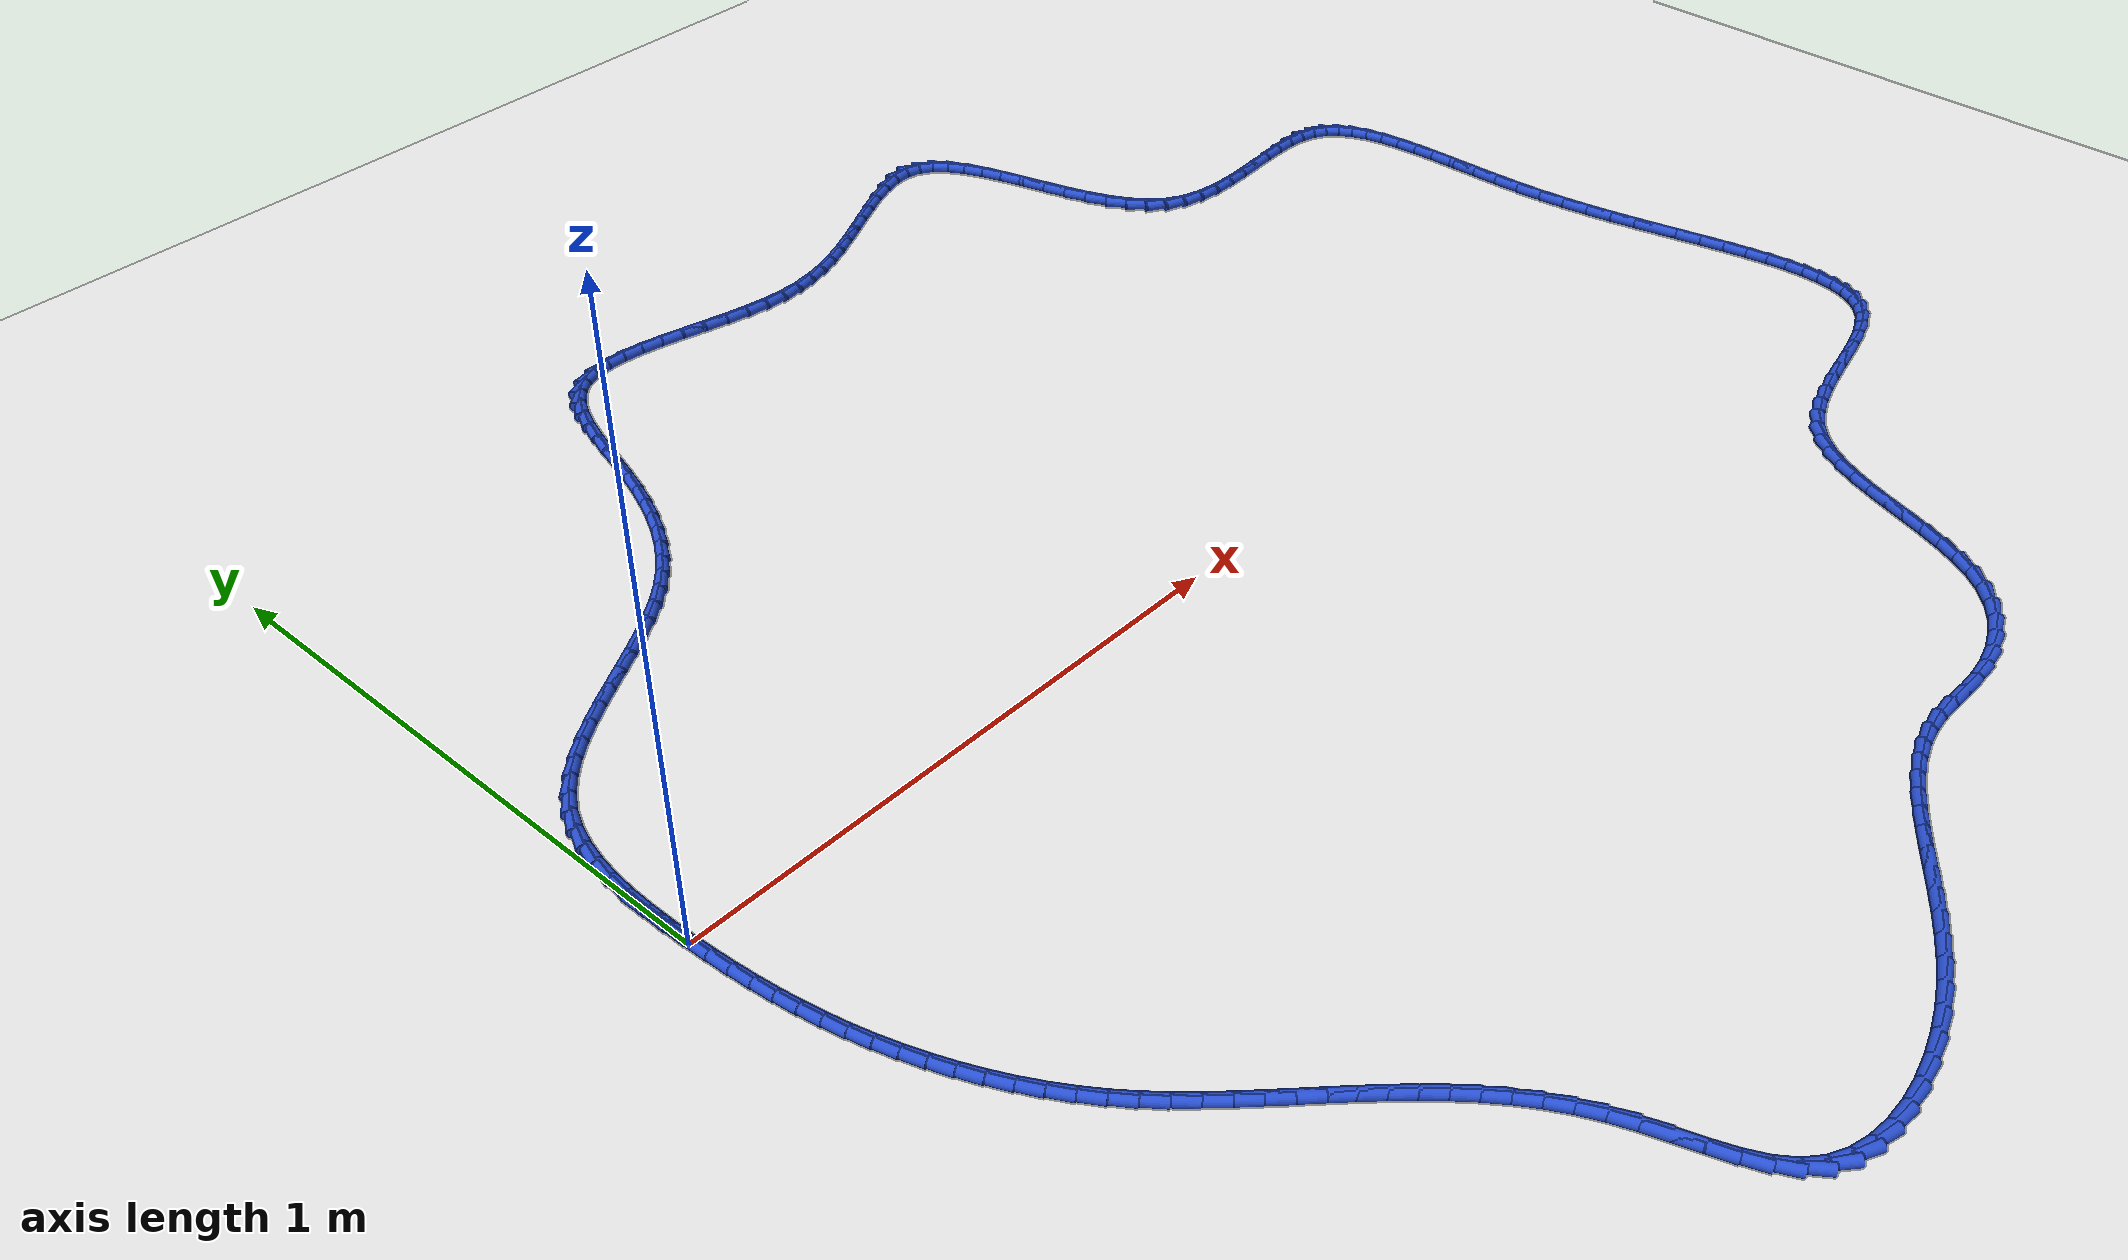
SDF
<sdf version="1.6">
 <world name="default">
  <light name="sun" type="directional">
   <pose>0 0 10 0 -0 0</pose>
   <diffuse>0.8 0.8 0.8 1</diffuse>
   <specular>0.2 0.2 0.2 1</specular>
   <attenuation>
    <range>1000</range>
    <constant>0.9</constant>
    <linear>0.01</linear>
    <quadratic>0.001</quadratic>
   </attenuation>
   <direction>-0.5 0.1 -0.9</direction>
  </light>
  <model name="ground_plane">
   <static>1</static>
   <link name="link">
    <collision name="collision">
     <geometry><plane><normal>0 0 1</normal><size>100 100</size></plane></geometry>
     <surface><friction><ode><mu>100</mu><mu2>50</mu2></ode></friction></surface>
    </collision>
    <visual name="visual">
     <cast_shadows>0</cast_shadows>
     <geometry><plane><normal>0 0 1</normal><size>100 100</size></plane></geometry>
     <material>
      <script><uri>file://media/materials/scripts/gazebo.material</uri><name>Gazebo/WhiteGlow</name></script>
     </material>
    </visual>
   </link>
  </model>
  <gravity>0 0 -9.8</gravity>
  <magnetic_field>6e-06 2.3e-05 -4.2e-05</magnetic_field>
  <atmosphere type="adiabatic"/>
  <physics name="default_physics" default="0" type="ode">
   <max_step_size>0.001</max_step_size>
   <real_time_factor>1</real_time_factor>
   <real_time_update_rate>1000</real_time_update_rate>
  </physics>
  <scene><ambient>0.4 0.4 0.4 1</ambient><background>0.7 0.7 0.7 1</background><shadows>1</shadows></scene>
  <spherical_coordinates>
   <surface_model>EARTH_WGS84</surface_model>
   <latitude_deg>0</latitude_deg>
   <longitude_deg>0</longitude_deg>
   <elevation>0</elevation>
   <heading_deg>0</heading_deg>
  </spherical_coordinates>
  <model name="line">
   <link name="link_0">
    <pose>3.037798962032823e-17 7.632783294297951e-17 0.01 0 1.57 -1.5330032600161192</pose>
    <collision name="collision">
     <geometry><cylinder><radius>0.01</radius><length>0.08</length></cylinder></geometry>
    </collision>
    <visual name="visual">
     <material>
      <script><name>Gazebo/Blue</name><uri>file://media/materials/scripts/gazebo.material</uri></script>
     </material>
     <geometry><cylinder><radius>0.01</radius><length>0.08</length></cylinder></geometry>
    </visual>
   </link>
   <link name="link_1">
    <pose>-0.0014637493535130366 0.03871219017194916 0.01 0 1.57 -1.5608747347800838</pose>
    <collision name="collision">
     <geometry><cylinder><radius>0.01</radius><length>0.08</length></cylinder></geometry>
    </collision>
    <visual name="visual">
     <material>
      <script><name>Gazebo/Blue</name><uri>file://media/materials/scripts/gazebo.material</uri></script>
     </material>
     <geometry><cylinder><radius>0.01</radius><length>0.08</length></cylinder></geometry>
    </visual>
   </link>
   <link name="link_2">
    <pose>-0.0018502820695263608 0.0776696510497378 0.01 0 1.57 1.5417352929323886</pose>
    <collision name="collision">
     <geometry><cylinder><radius>0.01</radius><length>0.08</length></cylinder></geometry>
    </collision>
    <visual name="visual">
     <material>
      <script><name>Gazebo/Blue</name><uri>file://media/materials/scripts/gazebo.material</uri></script>
     </material>
     <geometry><cylinder><radius>0.01</radius><length>0.08</length></cylinder></geometry>
    </visual>
   </link>
   <link name="link_3">
    <pose>-0.0007233850427675321 0.1164356418366415 0.01 0 1.57 1.4903015447215042</pose>
    <collision name="collision">
     <geometry><cylinder><radius>0.01</radius><length>0.08</length></cylinder></geometry>
    </collision>
    <visual name="visual">
     <material>
      <script><name>Gazebo/Blue</name><uri>file://media/materials/scripts/gazebo.material</uri></script>
     </material>
     <geometry><cylinder><radius>0.01</radius><length>0.08</length></cylinder></geometry>
    </visual>
   </link>
   <link name="link_4">
    <pose>0.0023531548320358626 0.15457342173593558 0.01 0 1.57 1.4245066033565696</pose>
    <collision name="collision">
     <geometry><cylinder><radius>0.01</radius><length>0.08</length></cylinder></geometry>
    </collision>
    <visual name="visual">
     <material>
      <script><name>Gazebo/Blue</name><uri>file://media/materials/scripts/gazebo.material</uri></script>
     </material>
     <geometry><cylinder><radius>0.01</radius><length>0.08</length></cylinder></geometry>
    </visual>
   </link>
   <link name="link_5">
    <pose>0.007815550660156234 0.19164624995089555 0.01 0 1.57 1.341976795140099</pose>
    <collision name="collision">
     <geometry><cylinder><radius>0.01</radius><length>0.08</length></cylinder></geometry>
    </collision>
    <visual name="visual">
     <material>
      <script><name>Gazebo/Blue</name><uri>file://media/materials/scripts/gazebo.material</uri></script>
     </material>
     <geometry><cylinder><radius>0.01</radius><length>0.08</length></cylinder></geometry>
    </visual>
   </link>
   <link name="link_6">
    <pose>0.016100015546866003 0.22721738568479677 0.01 0 1.57 1.240192116064011</pose>
    <collision name="collision">
     <geometry><cylinder><radius>0.01</radius><length>0.08</length></cylinder></geometry>
    </collision>
    <visual name="visual">
     <material>
      <script><name>Gazebo/Blue</name><uri>file://media/materials/scripts/gazebo.material</uri></script>
     </material>
     <geometry><cylinder><radius>0.01</radius><length>0.08</length></cylinder></geometry>
    </visual>
   </link>
   <link name="link_7">
    <pose>0.02764276259743758 0.26085008814091465 0.01 0 1.57 1.1172193816793705</pose>
    <collision name="collision">
     <geometry><cylinder><radius>0.01</radius><length>0.08</length></cylinder></geometry>
    </collision>
    <visual name="visual">
     <material>
      <script><name>Gazebo/Blue</name><uri>file://media/materials/scripts/gazebo.material</uri></script>
     </material>
     <geometry><cylinder><radius>0.01</radius><length>0.08</length></cylinder></geometry>
    </visual>
   </link>
   <link name="link_8">
    <pose>0.042880004917143354 0.2921076165225246 0.01 0 1.57 0.9776191270760713</pose>
    <collision name="collision">
     <geometry><cylinder><radius>0.01</radius><length>0.08</length></cylinder></geometry>
    </collision>
    <visual name="visual">
     <material>
      <script><name>Gazebo/Blue</name><uri>file://media/materials/scripts/gazebo.material</uri></script>
     </material>
     <geometry><cylinder><radius>0.01</radius><length>0.08</length></cylinder></geometry>
    </visual>
   </link>
   <link name="link_9">
    <pose>0.06212613755117945 0.3206556349424241 0.01 0 1.57 0.8487578918379707</pose>
    <collision name="collision">
     <geometry><cylinder><radius>0.01</radius><length>0.08</length></cylinder></geometry>
    </collision>
    <visual name="visual">
     <material>
      <script><name>Gazebo/Blue</name><uri>file://media/materials/scripts/gazebo.material</uri></script>
     </material>
     <geometry><cylinder><radius>0.01</radius><length>0.08</length></cylinder></geometry>
    </visual>
   </link>
   <link name="link_10">
    <pose>0.0850586770127533 0.34669519190882664 0.01 0 1.57 0.741772083795887</pose>
    <collision name="collision">
     <geometry><cylinder><radius>0.01</radius><length>0.08</length></cylinder></geometry>
    </collision>
    <visual name="visual">
     <material>
      <script><name>Gazebo/Blue</name><uri>file://media/materials/scripts/gazebo.material</uri></script>
     </material>
     <geometry><cylinder><radius>0.01</radius><length>0.08</length></cylinder></geometry>
    </visual>
   </link>
   <link name="link_11">
    <pose>0.11114769859648395 0.3706017189336433 0.01 0 1.57 0.6570114576614946</pose>
    <collision name="collision">
     <geometry><cylinder><radius>0.01</radius><length>0.08</length></cylinder></geometry>
    </collision>
    <visual name="visual">
     <material>
      <script><name>Gazebo/Blue</name><uri>file://media/materials/scripts/gazebo.material</uri></script>
     </material>
     <geometry><cylinder><radius>0.01</radius><length>0.08</length></cylinder></geometry>
    </visual>
   </link>
   <link name="link_12">
    <pose>0.13986316464976142 0.39275074247653496 0.01 0 1.57 0.5930588811222213</pose>
    <collision name="collision">
     <geometry><cylinder><radius>0.01</radius><length>0.08</length></cylinder></geometry>
    </collision>
    <visual name="visual">
     <material>
      <script><name>Gazebo/Blue</name><uri>file://media/materials/scripts/gazebo.material</uri></script>
     </material>
     <geometry><cylinder><radius>0.01</radius><length>0.08</length></cylinder></geometry>
    </visual>
   </link>
   <link name="link_13">
    <pose>0.17067503751997587 0.41351778899716307 0.01 0 1.57 0.5479621120039938</pose>
    <collision name="collision">
     <geometry><cylinder><radius>0.01</radius><length>0.08</length></cylinder></geometry>
    </collision>
    <visual name="visual">
     <material>
      <script><name>Gazebo/Blue</name><uri>file://media/materials/scripts/gazebo.material</uri></script>
     </material>
     <geometry><cylinder><radius>0.01</radius><length>0.08</length></cylinder></geometry>
    </visual>
   </link>
   <link name="link_14">
    <pose>0.20305327955451752 0.4332783849551887 0.01 0 1.57 0.519949568220709</pose>
    <collision name="collision">
     <geometry><cylinder><radius>0.01</radius><length>0.08</length></cylinder></geometry>
    </collision>
    <visual name="visual">
     <material>
      <script><name>Gazebo/Blue</name><uri>file://media/materials/scripts/gazebo.material</uri></script>
     </material>
     <geometry><cylinder><radius>0.01</radius><length>0.08</length></cylinder></geometry>
    </visual>
   </link>
   <link name="link_15">
    <pose>0.2364678531007762 0.452408056810273 0.01 0 1.57 0.5077593946100194</pose>
    <collision name="collision">
     <geometry><cylinder><radius>0.01</radius><length>0.08</length></cylinder></geometry>
    </collision>
    <visual name="visual">
     <material>
      <script><name>Gazebo/Blue</name><uri>file://media/materials/scripts/gazebo.material</uri></script>
     </material>
     <geometry><cylinder><radius>0.01</radius><length>0.08</length></cylinder></geometry>
    </visual>
   </link>
   <link name="link_16">
    <pose>0.27038872050614216 0.47128233102207734 0.01 0 1.57 0.5107580890191017</pose>
    <collision name="collision">
     <geometry><cylinder><radius>0.01</radius><length>0.08</length></cylinder></geometry>
    </collision>
    <visual name="visual">
     <material>
      <script><name>Gazebo/Blue</name><uri>file://media/materials/scripts/gazebo.material</uri></script>
     </material>
     <geometry><cylinder><radius>0.01</radius><length>0.08</length></cylinder></geometry>
    </visual>
   </link>
   <link name="link_17">
    <pose>0.3042858441180054 0.49027673405026273 0.01 0 1.57 0.5289640279757442</pose>
    <collision name="collision">
     <geometry><cylinder><radius>0.01</radius><length>0.08</length></cylinder></geometry>
    </collision>
    <visual name="visual">
     <material>
      <script><name>Gazebo/Blue</name><uri>file://media/materials/scripts/gazebo.material</uri></script>
     </material>
     <geometry><cylinder><radius>0.01</radius><length>0.08</length></cylinder></geometry>
    </visual>
   </link>
   <link name="link_18">
    <pose>0.33762918628375616 0.5097667923544904 0.01 0 1.57 0.5630238014019764</pose>
    <collision name="collision">
     <geometry><cylinder><radius>0.01</radius><length>0.08</length></cylinder></geometry>
    </collision>
    <visual name="visual">
     <material>
      <script><name>Gazebo/Blue</name><uri>file://media/materials/scripts/gazebo.material</uri></script>
     </material>
     <geometry><cylinder><radius>0.01</radius><length>0.08</length></cylinder></geometry>
    </visual>
   </link>
   <link name="link_19">
    <pose>0.36988870935078455 0.5301280323944216 0.01 0 1.57 0.6141338083603641</pose>
    <collision name="collision">
     <geometry><cylinder><radius>0.01</radius><length>0.08</length></cylinder></geometry>
    </collision>
    <visual name="visual">
     <material>
      <script><name>Gazebo/Blue</name><uri>file://media/materials/scripts/gazebo.material</uri></script>
     </material>
     <geometry><cylinder><radius>0.01</radius><length>0.08</length></cylinder></geometry>
    </visual>
   </link>
   <link name="link_20">
    <pose>0.4005343756664804 0.5517359806297175 0.01 0 1.57 0.6838467115630937</pose>
    <collision name="collision">
     <geometry><cylinder><radius>0.01</radius><length>0.08</length></cylinder></geometry>
    </collision>
    <visual name="visual">
     <material>
      <script><name>Gazebo/Blue</name><uri>file://media/materials/scripts/gazebo.material</uri></script>
     </material>
     <geometry><cylinder><radius>0.01</radius><length>0.08</length></cylinder></geometry>
    </visual>
   </link>
   <link name="link_21">
    <pose>0.42903614757823405 0.5749661635200393 0.01 0 1.57 0.770908550478392</pose>
    <collision name="collision">
     <geometry><cylinder><radius>0.01</radius><length>0.08</length></cylinder></geometry>
    </collision>
    <visual name="visual">
     <material>
      <script><name>Gazebo/Blue</name><uri>file://media/materials/scripts/gazebo.material</uri></script>
     </material>
     <geometry><cylinder><radius>0.01</radius><length>0.08</length></cylinder></geometry>
    </visual>
   </link>
   <link name="link_22">
    <pose>0.4549531795687781 0.6001428159855304 0.01 0 1.57 0.8601882639126027</pose>
    <collision name="collision">
     <geometry><cylinder><radius>0.01</radius><length>0.08</length></cylinder></geometry>
    </collision>
    <visual name="visual">
     <material>
      <script><name>Gazebo/Blue</name><uri>file://media/materials/scripts/gazebo.material</uri></script>
     </material>
     <geometry><cylinder><radius>0.01</radius><length>0.08</length></cylinder></geometry>
    </visual>
   </link>
   <link name="link_23">
    <pose>0.47833253883078214 0.6273095899784907 0.01 0 1.57 0.9445348197051252</pose>
    <collision name="collision">
     <geometry><cylinder><radius>0.01</radius><length>0.08</length></cylinder></geometry>
    </collision>
    <visual name="visual">
     <material>
      <script><name>Gazebo/Blue</name><uri>file://media/materials/scripts/gazebo.material</uri></script>
     </material>
     <geometry><cylinder><radius>0.01</radius><length>0.08</length></cylinder></geometry>
    </visual>
   </link>
   <link name="link_24">
    <pose>0.49938728730046567 0.6564146791923055 0.01 0 1.57 1.0221511630316906</pose>
    <collision name="collision">
     <geometry><cylinder><radius>0.01</radius><length>0.08</length></cylinder></geometry>
    </collision>
    <visual name="visual">
     <material>
      <script><name>Gazebo/Blue</name><uri>file://media/materials/scripts/gazebo.material</uri></script>
     </material>
     <geometry><cylinder><radius>0.01</radius><length>0.08</length></cylinder></geometry>
    </visual>
   </link>
   <link name="link_25">
    <pose>0.5183306250798064 0.6874061978656613 0.01 0 1.57 1.0918629190837077</pose>
    <collision name="collision">
     <geometry><cylinder><radius>0.01</radius><length>0.08</length></cylinder></geometry>
    </collision>
    <visual name="visual">
     <material>
      <script><name>Gazebo/Blue</name><uri>file://media/materials/scripts/gazebo.material</uri></script>
     </material>
     <geometry><cylinder><radius>0.01</radius><length>0.08</length></cylinder></geometry>
    </visual>
   </link>
   <link name="link_26">
    <pose>0.5353757522707808 0.7202322602372438 0.01 0 1.57 1.1530917639785747</pose>
    <collision name="collision">
     <geometry><cylinder><radius>0.01</radius><length>0.08</length></cylinder></geometry>
    </collision>
    <visual name="visual">
     <material>
      <script><name>Gazebo/Blue</name><uri>file://media/materials/scripts/gazebo.material</uri></script>
     </material>
     <geometry><cylinder><radius>0.01</radius><length>0.08</length></cylinder></geometry>
    </visual>
   </link>
   <link name="link_27">
    <pose>0.5507358689753663 0.7548409805457393 0.01 0 1.57 1.2057438698655853</pose>
    <collision name="collision">
     <geometry><cylinder><radius>0.01</radius><length>0.08</length></cylinder></geometry>
    </collision>
    <visual name="visual">
     <material>
      <script><name>Gazebo/Blue</name><uri>file://media/materials/scripts/gazebo.material</uri></script>
     </material>
     <geometry><cylinder><radius>0.01</radius><length>0.08</length></cylinder></geometry>
    </visual>
   </link>
   <link name="link_28">
    <pose>0.5646241752955398 0.7911804730298336 0.01 0 1.57 1.2500663424024685</pose>
    <collision name="collision">
     <geometry><cylinder><radius>0.01</radius><length>0.08</length></cylinder></geometry>
    </collision>
    <visual name="visual">
     <material>
      <script><name>Gazebo/Blue</name><uri>file://media/materials/scripts/gazebo.material</uri></script>
     </material>
     <geometry><cylinder><radius>0.01</radius><length>0.08</length></cylinder></geometry>
    </visual>
   </link>
   <link name="link_29">
    <pose>0.5772538713332779 0.8291988519282122 0.01 0 1.57 1.2842068708518093</pose>
    <collision name="collision">
     <geometry><cylinder><radius>0.01</radius><length>0.08</length></cylinder></geometry>
    </collision>
    <visual name="visual">
     <material>
      <script><name>Gazebo/Blue</name><uri>file://media/materials/scripts/gazebo.material</uri></script>
     </material>
     <geometry><cylinder><radius>0.01</radius><length>0.08</length></cylinder></geometry>
    </visual>
   </link>
   <link name="link_30">
    <pose>0.5888965675219416 0.8687054875771452 0.01 0 1.57 1.2970618909761122</pose>
    <collision name="collision">
     <geometry><cylinder><radius>0.01</radius><length>0.08</length></cylinder></geometry>
    </collision>
    <visual name="visual">
     <material>
      <script><name>Gazebo/Blue</name><uri>file://media/materials/scripts/gazebo.material</uri></script>
     </material>
     <geometry><cylinder><radius>0.01</radius><length>0.08</length></cylinder></geometry>
    </visual>
   </link>
   <link name="link_31">
    <pose>0.6001417166011884 0.9087547694579026 0.01 0 1.57 1.2857001644294996</pose>
    <collision name="collision">
     <geometry><cylinder><radius>0.01</radius><length>0.08</length></cylinder></geometry>
    </collision>
    <visual name="visual">
     <material>
      <script><name>Gazebo/Blue</name><uri>file://media/materials/scripts/gazebo.material</uri></script>
     </material>
     <geometry><cylinder><radius>0.01</radius><length>0.08</length></cylinder></geometry>
    </visual>
   </link>
   <link name="link_32">
    <pose>0.6116863606278912 0.9481455267531703 0.01 0 1.57 1.2483030399106823</pose>
    <collision name="collision">
     <geometry><cylinder><radius>0.01</radius><length>0.08</length></cylinder></geometry>
    </collision>
    <visual name="visual">
     <material>
      <script><name>Gazebo/Blue</name><uri>file://media/materials/scripts/gazebo.material</uri></script>
     </material>
     <geometry><cylinder><radius>0.01</radius><length>0.08</length></cylinder></geometry>
    </visual>
   </link>
   <link name="link_33">
    <pose>0.6242276271953653 0.9856763854682249 0.01 0 1.57 1.1791563897353796</pose>
    <collision name="collision">
     <geometry><cylinder><radius>0.01</radius><length>0.08</length></cylinder></geometry>
    </collision>
    <visual name="visual">
     <material>
      <script><name>Gazebo/Blue</name><uri>file://media/materials/scripts/gazebo.material</uri></script>
     </material>
     <geometry><cylinder><radius>0.01</radius><length>0.08</length></cylinder></geometry>
    </visual>
   </link>
   <link name="link_34">
    <pose>0.6384626438969254 1.0201459716083427 0.01 0 1.57 1.0676461958618828</pose>
    <collision name="collision">
     <geometry><cylinder><radius>0.01</radius><length>0.08</length></cylinder></geometry>
    </collision>
    <visual name="visual">
     <material>
      <script><name>Gazebo/Blue</name><uri>file://media/materials/scripts/gazebo.material</uri></script>
     </material>
     <geometry><cylinder><radius>0.01</radius><length>0.08</length></cylinder></geometry>
    </visual>
   </link>
   <link name="link_35">
    <pose>0.6550885383258874 1.050352911178801 0.01 0 1.57 0.8980407543806458</pose>
    <collision name="collision">
     <geometry><cylinder><radius>0.01</radius><length>0.08</length></cylinder></geometry>
    </collision>
    <visual name="visual">
     <material>
      <script><name>Gazebo/Blue</name><uri>file://media/materials/scripts/gazebo.material</uri></script>
     </material>
     <geometry><cylinder><radius>0.01</radius><length>0.08</length></cylinder></geometry>
    </visual>
   </link>
   <link name="link_36">
    <pose>0.6748024380755661 1.0750958301848768 0.01 0 1.57 0.6565532783768415</pose>
    <collision name="collision">
     <geometry><cylinder><radius>0.01</radius><length>0.08</length></cylinder></geometry>
    </collision>
    <visual name="visual">
     <material>
      <script><name>Gazebo/Blue</name><uri>file://media/materials/scripts/gazebo.material</uri></script>
     </material>
     <geometry><cylinder><radius>0.01</radius><length>0.08</length></cylinder></geometry>
    </visual>
   </link>
   <link name="link_37">
    <pose>0.6982896079878961 1.0931949683809796 0.01 0 1.57 0.38666025852919494</pose>
    <collision name="collision">
     <geometry><cylinder><radius>0.01</radius><length>0.08</length></cylinder></geometry>
    </collision>
    <visual name="visual">
     <material>
      <script><name>Gazebo/Blue</name><uri>file://media/materials/scripts/gazebo.material</uri></script>
     </material>
     <geometry><cylinder><radius>0.01</radius><length>0.08</length></cylinder></geometry>
    </visual>
   </link>
   <link name="link_38">
    <pose>0.7257406513950206 1.1043718311247186 0.01 0 1.57 0.16597585879908255</pose>
    <collision name="collision">
     <geometry><cylinder><radius>0.01</radius><length>0.08</length></cylinder></geometry>
    </collision>
    <visual name="visual">
     <material>
      <script><name>Gazebo/Blue</name><uri>file://media/materials/scripts/gazebo.material</uri></script>
     </material>
     <geometry><cylinder><radius>0.01</radius><length>0.08</length></cylinder></geometry>
    </visual>
   </link>
   <link name="link_39">
    <pose>0.7566835093931303 1.109555284095823 0.01 0 1.57 0.005996668947930194</pose>
    <collision name="collision">
     <geometry><cylinder><radius>0.01</radius><length>0.08</length></cylinder></geometry>
    </collision>
    <visual name="visual">
     <material>
      <script><name>Gazebo/Blue</name><uri>file://media/materials/scripts/gazebo.material</uri></script>
     </material>
     <geometry><cylinder><radius>0.01</radius><length>0.08</length></cylinder></geometry>
    </visual>
   </link>
   <link name="link_40">
    <pose>0.7905997571135505 1.1097586710432983 0.01 0 1.57 -0.10310326478007036</pose>
    <collision name="collision">
     <geometry><cylinder><radius>0.01</radius><length>0.08</length></cylinder></geometry>
    </collision>
    <visual name="visual">
     <material>
      <script><name>Gazebo/Blue</name><uri>file://media/materials/scripts/gazebo.material</uri></script>
     </material>
     <geometry><cylinder><radius>0.01</radius><length>0.08</length></cylinder></geometry>
    </visual>
   </link>
   <link name="link_41">
    <pose>0.8269709696876066 1.1059953357161494 0.01 0 1.57 -0.1735713027183427</pose>
    <collision name="collision">
     <geometry><cylinder><radius>0.01</radius><length>0.08</length></cylinder></geometry>
    </collision>
    <visual name="visual">
     <material>
      <script><name>Gazebo/Blue</name><uri>file://media/materials/scripts/gazebo.material</uri></script>
     </material>
     <geometry><cylinder><radius>0.01</radius><length>0.08</length></cylinder></geometry>
    </visual>
   </link>
   <link name="link_42">
    <pose>0.8652787222466239 1.0992786218633823 0.01 0 1.57 -0.21455795697249452</pose>
    <collision name="collision">
     <geometry><cylinder><radius>0.01</radius><length>0.08</length></cylinder></geometry>
    </collision>
    <visual name="visual">
     <material>
      <script><name>Gazebo/Blue</name><uri>file://media/materials/scripts/gazebo.material</uri></script>
     </material>
     <geometry><cylinder><radius>0.01</radius><length>0.08</length></cylinder></geometry>
    </visual>
   </link>
   <link name="link_43">
    <pose>0.9050045899219278 1.0906218732340014 0.01 0 1.57 -0.23166166934272933</pose>
    <collision name="collision">
     <geometry><cylinder><radius>0.01</radius><length>0.08</length></cylinder></geometry>
    </collision>
    <visual name="visual">
     <material>
      <script><name>Gazebo/Blue</name><uri>file://media/materials/scripts/gazebo.material</uri></script>
     </material>
     <geometry><cylinder><radius>0.01</radius><length>0.08</length></cylinder></geometry>
    </visual>
   </link>
   <link name="link_44">
    <pose>0.9456301478448437 1.0810384335770127 0.01 0 1.57 -0.2275783645934718</pose>
    <collision name="collision">
     <geometry><cylinder><radius>0.01</radius><length>0.08</length></cylinder></geometry>
    </collision>
    <visual name="visual">
     <material>
      <script><name>Gazebo/Blue</name><uri>file://media/materials/scripts/gazebo.material</uri></script>
     </material>
     <geometry><cylinder><radius>0.01</radius><length>0.08</length></cylinder></geometry>
    </visual>
   </link>
   <link name="link_45">
    <pose>0.9866369711466966 1.0715416466414212 0.01 0 1.57 -0.20263318118459986</pose>
    <collision name="collision">
     <geometry><cylinder><radius>0.01</radius><length>0.08</length></cylinder></geometry>
    </collision>
    <visual name="visual">
     <material>
      <script><name>Gazebo/Blue</name><uri>file://media/materials/scripts/gazebo.material</uri></script>
     </material>
     <geometry><cylinder><radius>0.01</radius><length>0.08</length></cylinder></geometry>
    </visual>
   </link>
   <link name="link_46">
    <pose>1.027506634958812 1.0631448561762313 0.01 0 1.57 -0.15499674996213622</pose>
    <collision name="collision">
     <geometry><cylinder><radius>0.01</radius><length>0.08</length></cylinder></geometry>
    </collision>
    <visual name="visual">
     <material>
      <script><name>Gazebo/Blue</name><uri>file://media/materials/scripts/gazebo.material</uri></script>
     </material>
     <geometry><cylinder><radius>0.01</radius><length>0.08</length></cylinder></geometry>
    </visual>
   </link>
   <link name="link_47">
    <pose>1.0677207144125154 1.0568614059304497 0.01 0 1.57 -0.08068410687579954</pose>
    <collision name="collision">
     <geometry><cylinder><radius>0.01</radius><length>0.08</length></cylinder></geometry>
    </collision>
    <visual name="visual">
     <material>
      <script><name>Gazebo/Blue</name><uri>file://media/materials/scripts/gazebo.material</uri></script>
     </material>
     <geometry><cylinder><radius>0.01</radius><length>0.08</length></cylinder></geometry>
    </visual>
   </link>
   <link name="link_48">
    <pose>1.1067607846391323 1.053704639653081 0.01 0 1.57 0.023153118692723625</pose>
    <collision name="collision">
     <geometry><cylinder><radius>0.01</radius><length>0.08</length></cylinder></geometry>
    </collision>
    <visual name="visual">
     <material>
      <script><name>Gazebo/Blue</name><uri>file://media/materials/scripts/gazebo.material</uri></script>
     </material>
     <geometry><cylinder><radius>0.01</radius><length>0.08</length></cylinder></geometry>
    </visual>
   </link>
   <link name="link_49">
    <pose>1.1441759204244601 1.05457107156018 0.01 0 1.57 0.13381082758630672</pose>
    <collision name="collision">
     <geometry><cylinder><radius>0.01</radius><length>0.08</length></cylinder></geometry>
    </collision>
    <visual name="visual">
     <material>
      <script><name>Gazebo/Blue</name><uri>file://media/materials/scripts/gazebo.material</uri></script>
     </material>
     <geometry><cylinder><radius>0.01</radius><length>0.08</length></cylinder></geometry>
    </visual>
   </link>
   <link name="link_50">
    <pose>1.1800667789540844 1.0594025278082169 0.01 0 1.57 0.2337774680418277</pose>
    <collision name="collision">
     <geometry><cylinder><radius>0.01</radius><length>0.08</length></cylinder></geometry>
    </collision>
    <visual name="visual">
     <material>
      <script><name>Gazebo/Blue</name><uri>file://media/materials/scripts/gazebo.material</uri></script>
     </material>
     <geometry><cylinder><radius>0.01</radius><length>0.08</length></cylinder></geometry>
    </visual>
   </link>
   <link name="link_51">
    <pose>1.2148034874800648 1.0676744312475028 0.01 0 1.57 0.31820620352649354</pose>
    <collision name="collision">
     <geometry><cylinder><radius>0.01</radius><length>0.08</length></cylinder></geometry>
    </collision>
    <visual name="visual">
     <material>
      <script><name>Gazebo/Blue</name><uri>file://media/materials/scripts/gazebo.material</uri></script>
     </material>
     <geometry><cylinder><radius>0.01</radius><length>0.08</length></cylinder></geometry>
    </visual>
   </link>
   <link name="link_52">
    <pose>1.2487580010700439 1.0788590411145178 0.01 0 1.57 0.384403145789395</pose>
    <collision name="collision">
     <geometry><cylinder><radius>0.01</radius><length>0.08</length></cylinder></geometry>
    </collision>
    <visual name="visual">
     <material>
      <script><name>Gazebo/Blue</name><uri>file://media/materials/scripts/gazebo.material</uri></script>
     </material>
     <geometry><cylinder><radius>0.01</radius><length>0.08</length></cylinder></geometry>
    </visual>
   </link>
   <link name="link_53">
    <pose>1.2823022747916633 1.0924286166457402 0.01 0 1.57 0.4314846699349305</pose>
    <collision name="collision">
     <geometry><cylinder><radius>0.01</radius><length>0.08</length></cylinder></geometry>
    </collision>
    <visual name="visual">
     <material>
      <script><name>Gazebo/Blue</name><uri>file://media/materials/scripts/gazebo.material</uri></script>
     </material>
     <geometry><cylinder><radius>0.01</radius><length>0.08</length></cylinder></geometry>
    </visual>
   </link>
   <link name="link_54">
    <pose>1.3158082637125625 1.1078554170776491 0.01 0 1.57 0.45977378798092217</pose>
    <collision name="collision">
     <geometry><cylinder><radius>0.01</radius><length>0.08</length></cylinder></geometry>
    </collision>
    <visual name="visual">
     <material>
      <script><name>Gazebo/Blue</name><uri>file://media/materials/scripts/gazebo.material</uri></script>
     </material>
     <geometry><cylinder><radius>0.01</radius><length>0.08</length></cylinder></geometry>
    </visual>
   </link>
   <link name="link_55">
    <pose>1.3496479229003844 1.1246117016467234 0.01 0 1.57 0.47023471055390703</pose>
    <collision name="collision">
     <geometry><cylinder><radius>0.01</radius><length>0.08</length></cylinder></geometry>
    </collision>
    <visual name="visual">
     <material>
      <script><name>Gazebo/Blue</name><uri>file://media/materials/scripts/gazebo.material</uri></script>
     </material>
     <geometry><cylinder><radius>0.01</radius><length>0.08</length></cylinder></geometry>
    </visual>
   </link>
   <link name="link_56">
    <pose>1.3841932074227694 1.1421697295894424 0.01 0 1.57 0.4641100833375244</pose>
    <collision name="collision">
     <geometry><cylinder><radius>0.01</radius><length>0.08</length></cylinder></geometry>
    </collision>
    <visual name="visual">
     <material>
      <script><name>Gazebo/Blue</name><uri>file://media/materials/scripts/gazebo.material</uri></script>
     </material>
     <geometry><cylinder><radius>0.01</radius><length>0.08</length></cylinder></geometry>
    </visual>
   </link>
   <link name="link_57">
    <pose>1.4198160723473592 1.160001760142285 0.01 0 1.57 0.4411880590642523</pose>
    <collision name="collision">
     <geometry><cylinder><radius>0.01</radius><length>0.08</length></cylinder></geometry>
    </collision>
    <visual name="visual">
     <material>
      <script><name>Gazebo/Blue</name><uri>file://media/materials/scripts/gazebo.material</uri></script>
     </material>
     <geometry><cylinder><radius>0.01</radius><length>0.08</length></cylinder></geometry>
    </visual>
   </link>
   <link name="link_58">
    <pose>1.4567373012334133 1.177437172259663 0.01 0 1.57 0.38779277143367824</pose>
    <collision name="collision">
     <geometry><cylinder><radius>0.01</radius><length>0.08</length></cylinder></geometry>
    </collision>
    <visual name="visual">
     <material>
      <script><name>Gazebo/Blue</name><uri>file://media/materials/scripts/gazebo.material</uri></script>
     </material>
     <geometry><cylinder><radius>0.01</radius><length>0.08</length></cylinder></geometry>
    </visual>
   </link>
   <link name="link_59">
    <pose>1.4939364080450266 1.1926321545787328 0.01 0 1.57 0.2858420872469127</pose>
    <collision name="collision">
     <geometry><cylinder><radius>0.01</radius><length>0.08</length></cylinder></geometry>
    </collision>
    <visual name="visual">
     <material>
      <script><name>Gazebo/Blue</name><uri>file://media/materials/scripts/gazebo.material</uri></script>
     </material>
     <geometry><cylinder><radius>0.01</radius><length>0.08</length></cylinder></geometry>
    </visual>
   </link>
   <link name="link_60">
    <pose>1.5297840384328139 1.2031674217117962 0.01 0 1.57 0.10466865321659184</pose>
    <collision name="collision">
     <geometry><cylinder><radius>0.01</radius><length>0.08</length></cylinder></geometry>
    </collision>
    <visual name="visual">
     <material>
      <script><name>Gazebo/Blue</name><uri>file://media/materials/scripts/gazebo.material</uri></script>
     </material>
     <geometry><cylinder><radius>0.01</radius><length>0.08</length></cylinder></geometry>
    </visual>
   </link>
   <link name="link_61">
    <pose>1.5626466423360947 1.206619722679889 0.01 0 1.57 -0.20090752166121828</pose>
    <collision name="collision">
     <geometry><cylinder><radius>0.01</radius><length>0.08</length></cylinder></geometry>
    </collision>
    <visual name="visual">
     <material>
      <script><name>Gazebo/Blue</name><uri>file://media/materials/scripts/gazebo.material</uri></script>
     </material>
     <geometry><cylinder><radius>0.01</radius><length>0.08</length></cylinder></geometry>
    </visual>
   </link>
   <link name="link_62">
    <pose>1.5910601172253214 1.2008331758100141 0.01 0 1.57 -0.556878112638074</pose>
    <collision name="collision">
     <geometry><cylinder><radius>0.01</radius><length>0.08</length></cylinder></geometry>
    </collision>
    <visual name="visual">
     <material>
      <script><name>Gazebo/Blue</name><uri>file://media/materials/scripts/gazebo.material</uri></script>
     </material>
     <geometry><cylinder><radius>0.01</radius><length>0.08</length></cylinder></geometry>
    </visual>
   </link>
   <link name="link_63">
    <pose>1.6150020444992763 1.1859267158797964 0.01 0 1.57 -0.8454522377044399</pose>
    <collision name="collision">
     <geometry><cylinder><radius>0.01</radius><length>0.08</length></cylinder></geometry>
    </collision>
    <visual name="visual">
     <material>
      <script><name>Gazebo/Blue</name><uri>file://media/materials/scripts/gazebo.material</uri></script>
     </material>
     <geometry><cylinder><radius>0.01</radius><length>0.08</length></cylinder></geometry>
    </visual>
   </link>
   <link name="link_64">
    <pose>1.63517850366277 1.1631687664301624 0.01 0 1.57 -1.042409784000581</pose>
    <collision name="collision">
     <geometry><cylinder><radius>0.01</radius><length>0.08</length></cylinder></geometry>
    </collision>
    <visual name="visual">
     <material>
      <script><name>Gazebo/Blue</name><uri>file://media/materials/scripts/gazebo.material</uri></script>
     </material>
     <geometry><cylinder><radius>0.01</radius><length>0.08</length></cylinder></geometry>
    </visual>
   </link>
   <link name="link_65">
    <pose>1.652301194533826 1.1338366192294627 0.01 0 1.57 -1.167379028693601</pose>
    <collision name="collision">
     <geometry><cylinder><radius>0.01</radius><length>0.08</length></cylinder></geometry>
    </collision>
    <visual name="visual">
     <material>
      <script><name>Gazebo/Blue</name><uri>file://media/materials/scripts/gazebo.material</uri></script>
     </material>
     <geometry><cylinder><radius>0.01</radius><length>0.08</length></cylinder></geometry>
    </visual>
   </link>
   <link name="link_66">
    <pose>1.667081816930466 1.0992075660460463 0.01 0 1.57 -1.2428327068350764</pose>
    <collision name="collision">
     <geometry><cylinder><radius>0.01</radius><length>0.08</length></cylinder></geometry>
    </collision>
    <visual name="visual">
     <material>
      <script><name>Gazebo/Blue</name><uri>file://media/materials/scripts/gazebo.material</uri></script>
     </material>
     <geometry><cylinder><radius>0.01</radius><length>0.08</length></cylinder></geometry>
    </visual>
   </link>
   <link name="link_67">
    <pose>1.6802320706707132 1.060558898648265 0.01 0 1.57 -1.2834609056424273</pose>
    <collision name="collision">
     <geometry><cylinder><radius>0.01</radius><length>0.08</length></cylinder></geometry>
    </collision>
    <visual name="visual">
     <material>
      <script><name>Gazebo/Blue</name><uri>file://media/materials/scripts/gazebo.material</uri></script>
     </material>
     <geometry><cylinder><radius>0.01</radius><length>0.08</length></cylinder></geometry>
    </visual>
   </link>
   <link name="link_68">
    <pose>1.6924636555725903 1.0191679088044683 0.01 0 1.57 -1.2972482779270065</pose>
    <collision name="collision">
     <geometry><cylinder><radius>0.01</radius><length>0.08</length></cylinder></geometry>
    </collision>
    <visual name="visual">
     <material>
      <script><name>Gazebo/Blue</name><uri>file://media/materials/scripts/gazebo.material</uri></script>
     </material>
     <geometry><cylinder><radius>0.01</radius><length>0.08</length></cylinder></geometry>
    </visual>
   </link>
   <link name="link_69">
    <pose>1.7044882714541203 0.9763118882830061 0.01 0 1.57 -1.2875393513096767</pose>
    <collision name="collision">
     <geometry><cylinder><radius>0.01</radius><length>0.08</length></cylinder></geometry>
    </collision>
    <visual name="visual">
     <material>
      <script><name>Gazebo/Blue</name><uri>file://media/materials/scripts/gazebo.material</uri></script>
     </material>
     <geometry><cylinder><radius>0.01</radius><length>0.08</length></cylinder></geometry>
    </visual>
   </link>
   <link name="link_70">
    <pose>1.7170176181333245 0.9332681288522294 0.01 0 1.57 -1.2541806238959856</pose>
    <collision name="collision">
     <geometry><cylinder><radius>0.01</radius><length>0.08</length></cylinder></geometry>
    </collision>
    <visual name="visual">
     <material>
      <script><name>Gazebo/Blue</name><uri>file://media/materials/scripts/gazebo.material</uri></script>
     </material>
     <geometry><cylinder><radius>0.01</radius><length>0.08</length></cylinder></geometry>
    </visual>
   </link>
   <link name="link_71">
    <pose>1.7307633954282269 0.8913139222804881 0.01 0 1.57 -1.1938016632790547</pose>
    <collision name="collision">
     <geometry><cylinder><radius>0.01</radius><length>0.08</length></cylinder></geometry>
    </collision>
    <visual name="visual">
     <material>
      <script><name>Gazebo/Blue</name><uri>file://media/materials/scripts/gazebo.material</uri></script>
     </material>
     <geometry><cylinder><radius>0.01</radius><length>0.08</length></cylinder></geometry>
    </visual>
   </link>
   <link name="link_72">
    <pose>1.746437303156849 0.8517265603361323 0.01 0 1.57 -1.0995629544573708</pose>
    <collision name="collision">
     <geometry><cylinder><radius>0.01</radius><length>0.08</length></cylinder></geometry>
    </collision>
    <visual name="visual">
     <material>
      <script><name>Gazebo/Blue</name><uri>file://media/materials/scripts/gazebo.material</uri></script>
     </material>
     <geometry><cylinder><radius>0.01</radius><length>0.08</length></cylinder></geometry>
    </visual>
   </link>
   <link name="link_73">
    <pose>1.7647510411372147 0.8157833347875121 0.01 0 1.57 -0.9611526923810393</pose>
    <collision name="collision">
     <geometry><cylinder><radius>0.01</radius><length>0.08</length></cylinder></geometry>
    </collision>
    <visual name="visual">
     <material>
      <script><name>Gazebo/Blue</name><uri>file://media/materials/scripts/gazebo.material</uri></script>
     </material>
     <geometry><cylinder><radius>0.01</radius><length>0.08</length></cylinder></geometry>
    </visual>
   </link>
   <link name="link_74">
    <pose>1.7864163091873455 0.7847615374029782 0.01 0 1.57 -0.767489251983084</pose>
    <collision name="collision">
     <geometry><cylinder><radius>0.01</radius><length>0.08</length></cylinder></geometry>
    </collision>
    <visual name="visual">
     <material>
      <script><name>Gazebo/Blue</name><uri>file://media/materials/scripts/gazebo.material</uri></script>
     </material>
     <geometry><cylinder><radius>0.01</radius><length>0.08</length></cylinder></geometry>
    </visual>
   </link>
   <link name="link_75">
    <pose>1.8121448071252642 0.7599384599508806 0.01 0 1.57 -0.5262528285061314</pose>
    <collision name="collision">
     <geometry><cylinder><radius>0.01</radius><length>0.08</length></cylinder></geometry>
    </collision>
    <visual name="visual">
     <material>
      <script><name>Gazebo/Blue</name><uri>file://media/materials/scripts/gazebo.material</uri></script>
     </material>
     <geometry><cylinder><radius>0.01</radius><length>0.08</length></cylinder></geometry>
    </visual>
   </link>
   <link name="link_76">
    <pose>1.842471889548279 0.7423216262222947 0.01 0 1.57 -0.31054921585594547</pose>
    <collision name="collision">
     <geometry><cylinder><radius>0.01</radius><length>0.08</length></cylinder></geometry>
    </collision>
    <visual name="visual">
     <material>
      <script><name>Gazebo/Blue</name><uri>file://media/materials/scripts/gazebo.material</uri></script>
     </material>
     <geometry><cylinder><radius>0.01</radius><length>0.08</length></cylinder></geometry>
    </visual>
   </link>
   <link name="link_77">
    <pose>1.8768643711742834 0.7312839376423638 0.01 0 1.57 -0.1506994818354576</pose>
    <collision name="collision">
     <geometry><cylinder><radius>0.01</radius><length>0.08</length></cylinder></geometry>
    </collision>
    <visual name="visual">
     <material>
      <script><name>Gazebo/Blue</name><uri>file://media/materials/scripts/gazebo.material</uri></script>
     </material>
     <geometry><cylinder><radius>0.01</radius><length>0.08</length></cylinder></geometry>
    </visual>
   </link>
   <link name="link_78">
    <pose>1.9143887084472733 0.7255858387672719 0.01 0 1.57 -0.04023668969716423</pose>
    <collision name="collision">
     <geometry><cylinder><radius>0.01</radius><length>0.08</length></cylinder></geometry>
    </collision>
    <visual name="visual">
     <material>
      <script><name>Gazebo/Blue</name><uri>file://media/materials/scripts/gazebo.material</uri></script>
     </material>
     <geometry><cylinder><radius>0.01</radius><length>0.08</length></cylinder></geometry>
    </visual>
   </link>
   <link name="link_79">
    <pose>1.9541106531050751 0.7239866961134542 0.01 0 1.57 0.030713060975538498</pose>
    <collision name="collision">
     <geometry><cylinder><radius>0.01</radius><length>0.08</length></cylinder></geometry>
    </collision>
    <visual name="visual">
     <material>
      <script><name>Gazebo/Blue</name><uri>file://media/materials/scripts/gazebo.material</uri></script>
     </material>
     <geometry><cylinder><radius>0.01</radius><length>0.08</length></cylinder></geometry>
    </visual>
   </link>
   <link name="link_80">
    <pose>1.9950959568855162 0.7252458761973456 0.01 0 1.57 0.06952132871976674</pose>
    <collision name="collision">
     <geometry><cylinder><radius>0.01</radius><length>0.08</length></cylinder></geometry>
    </collision>
    <visual name="visual">
     <material>
      <script><name>Gazebo/Blue</name><uri>file://media/materials/scripts/gazebo.material</uri></script>
     </material>
     <geometry><cylinder><radius>0.01</radius><length>0.08</length></cylinder></geometry>
    </visual>
   </link>
   <link name="link_81">
    <pose>2.0364103715264235 0.7281227455353816 0.01 0 1.57 0.07976122567753044</pose>
    <collision name="collision">
     <geometry><cylinder><radius>0.01</radius><length>0.08</length></cylinder></geometry>
    </collision>
    <visual name="visual">
     <material>
      <script><name>Gazebo/Blue</name><uri>file://media/materials/scripts/gazebo.material</uri></script>
     </material>
     <geometry><cylinder><radius>0.01</radius><length>0.08</length></cylinder></geometry>
    </visual>
   </link>
   <link name="link_82">
    <pose>2.0771196487656236 0.731376670643997 0.01 0 1.57 0.06094953654843173</pose>
    <collision name="collision">
     <geometry><cylinder><radius>0.01</radius><length>0.08</length></cylinder></geometry>
    </collision>
    <visual name="visual">
     <material>
      <script><name>Gazebo/Blue</name><uri>file://media/materials/scripts/gazebo.material</uri></script>
     </material>
     <geometry><cylinder><radius>0.01</radius><length>0.08</length></cylinder></geometry>
    </visual>
   </link>
   <link name="link_83">
    <pose>2.116289540340944 0.7337670180396269 0.01 0 1.57 0.007797263770574063</pose>
    <collision name="collision">
     <geometry><cylinder><radius>0.01</radius><length>0.08</length></cylinder></geometry>
    </collision>
    <visual name="visual">
     <material>
      <script><name>Gazebo/Blue</name><uri>file://media/materials/scripts/gazebo.material</uri></script>
     </material>
     <geometry><cylinder><radius>0.01</radius><length>0.08</length></cylinder></geometry>
    </visual>
   </link>
   <link name="link_84">
    <pose>2.152985797990211 0.7340531542387062 0.01 0 1.57 -0.09162789334053047</pose>
    <collision name="collision">
     <geometry><cylinder><radius>0.01</radius><length>0.08</length></cylinder></geometry>
    </collision>
    <visual name="visual">
     <material>
      <script><name>Gazebo/Blue</name><uri>file://media/materials/scripts/gazebo.material</uri></script>
     </material>
     <geometry><cylinder><radius>0.01</radius><length>0.08</length></cylinder></geometry>
    </visual>
   </link>
   <link name="link_85">
    <pose>2.186274173451253 0.7309944457576701 0.01 0 1.57 -0.25818791324638857</pose>
    <collision name="collision">
     <geometry><cylinder><radius>0.01</radius><length>0.08</length></cylinder></geometry>
    </collision>
    <visual name="visual">
     <material>
      <script><name>Gazebo/Blue</name><uri>file://media/materials/scripts/gazebo.material</uri></script>
     </material>
     <geometry><cylinder><radius>0.01</radius><length>0.08</length></cylinder></geometry>
    </visual>
   </link>
   <link name="link_86">
    <pose>2.2152204184618953 0.723350259112954 0.01 0 1.57 -0.505108137282745</pose>
    <collision name="collision">
     <geometry><cylinder><radius>0.01</radius><length>0.08</length></cylinder></geometry>
    </collision>
    <visual name="visual">
     <material>
      <script><name>Gazebo/Blue</name><uri>file://media/materials/scripts/gazebo.material</uri></script>
     </material>
     <geometry><cylinder><radius>0.01</radius><length>0.08</length></cylinder></geometry>
    </visual>
   </link>
   <link name="link_87">
    <pose>2.239116142775662 0.7101370287173564 0.01 0 1.57 -0.77235794175562</pose>
    <collision name="collision">
     <geometry><cylinder><radius>0.01</radius><length>0.08</length></cylinder></geometry>
    </collision>
    <visual name="visual">
     <material>
      <script><name>Gazebo/Blue</name><uri>file://media/materials/scripts/gazebo.material</uri></script>
     </material>
     <geometry><cylinder><radius>0.01</radius><length>0.08</length></cylinder></geometry>
    </visual>
   </link>
   <link name="link_88">
    <pose>2.25824516529959 0.6915005052005955 0.01 0 1.57 -1.007155816850309</pose>
    <collision name="collision">
     <geometry><cylinder><radius>0.01</radius><length>0.08</length></cylinder></geometry>
    </collision>
    <visual name="visual">
     <material>
      <script><name>Gazebo/Blue</name><uri>file://media/materials/scripts/gazebo.material</uri></script>
     </material>
     <geometry><cylinder><radius>0.01</radius><length>0.08</length></cylinder></geometry>
    </visual>
   </link>
   <link name="link_89">
    <pose>2.2731636899331837 0.667896463332109 0.01 0 1.57 -1.1897403893151393</pose>
    <collision name="collision">
     <geometry><cylinder><radius>0.01</radius><length>0.08</length></cylinder></geometry>
    </collision>
    <visual name="visual">
     <material>
      <script><name>Gazebo/Blue</name><uri>file://media/materials/scripts/gazebo.material</uri></script>
     </material>
     <geometry><cylinder><radius>0.01</radius><length>0.08</length></cylinder></geometry>
    </visual>
   </link>
   <link name="link_90">
    <pose>2.284427928139857 0.6397806864904517 0.01 0 1.57 -1.3222158271903168</pose>
    <collision name="collision">
     <geometry><cylinder><radius>0.01</radius><length>0.08</length></cylinder></geometry>
    </collision>
    <visual name="visual">
     <material>
      <script><name>Gazebo/Blue</name><uri>file://media/materials/scripts/gazebo.material</uri></script>
     </material>
     <geometry><cylinder><radius>0.01</radius><length>0.08</length></cylinder></geometry>
    </visual>
   </link>
   <link name="link_91">
    <pose>2.2925940913830236 0.607608958054178 0.01 0 1.57 -1.4148462364554462</pose>
    <collision name="collision">
     <geometry><cylinder><radius>0.01</radius><length>0.08</length></cylinder></geometry>
    </collision>
    <visual name="visual">
     <material>
      <script><name>Gazebo/Blue</name><uri>file://media/materials/scripts/gazebo.material</uri></script>
     </material>
     <geometry><cylinder><radius>0.01</radius><length>0.08</length></cylinder></geometry>
    </visual>
   </link>
   <link name="link_92">
    <pose>2.2982183911261 0.5718370614018435 0.01 0 1.57 -1.4775680002436946</pose>
    <collision name="collision">
     <geometry><cylinder><radius>0.01</radius><length>0.08</length></cylinder></geometry>
    </collision>
    <visual name="visual">
     <material>
      <script><name>Gazebo/Blue</name><uri>file://media/materials/scripts/gazebo.material</uri></script>
     </material>
     <geometry><cylinder><radius>0.01</radius><length>0.08</length></cylinder></geometry>
    </visual>
   </link>
   <link name="link_93">
    <pose>2.301857038832497 0.5329207799120032 0.01 0 1.57 -1.5177464408770602</pose>
    <collision name="collision">
     <geometry><cylinder><radius>0.01</radius><length>0.08</length></cylinder></geometry>
    </collision>
    <visual name="visual">
     <material>
      <script><name>Gazebo/Blue</name><uri>file://media/materials/scripts/gazebo.material</uri></script>
     </material>
     <geometry><cylinder><radius>0.01</radius><length>0.08</length></cylinder></geometry>
    </visual>
   </link>
   <link name="link_94">
    <pose>2.3040662459656303 0.49131589696321176 0.01 0 1.57 -1.5403302069558267</pose>
    <collision name="collision">
     <geometry><cylinder><radius>0.01</radius><length>0.08</length></cylinder></geometry>
    </collision>
    <visual name="visual">
     <material>
      <script><name>Gazebo/Blue</name><uri>file://media/materials/scripts/gazebo.material</uri></script>
     </material>
     <geometry><cylinder><radius>0.01</radius><length>0.08</length></cylinder></geometry>
    </visual>
   </link>
   <link name="link_95">
    <pose>2.3054022239889136 0.4474781959340236 0.01 0 1.57 -1.5484616377362115</pose>
    <collision name="collision">
     <geometry><cylinder><radius>0.01</radius><length>0.08</length></cylinder></geometry>
    </collision>
    <visual name="visual">
     <material>
      <script><name>Gazebo/Blue</name><uri>file://media/materials/scripts/gazebo.material</uri></script>
     </material>
     <geometry><cylinder><radius>0.01</radius><length>0.08</length></cylinder></geometry>
    </visual>
   </link>
   <link name="link_96">
    <pose>2.306421184365761 0.4018634602029947 0.01 0 1.57 -1.5439969974416188</pose>
    <collision name="collision">
     <geometry><cylinder><radius>0.01</radius><length>0.08</length></cylinder></geometry>
    </collision>
    <visual name="visual">
     <material>
      <script><name>Gazebo/Blue</name><uri>file://media/materials/scripts/gazebo.material</uri></script>
     </material>
     <geometry><cylinder><radius>0.01</radius><length>0.08</length></cylinder></geometry>
    </visual>
   </link>
   <link name="link_97">
    <pose>2.3076793385595877 0.3549274731486797 0.01 0 1.57 -1.5278625387578928</pose>
    <collision name="collision">
     <geometry><cylinder><radius>0.01</radius><length>0.08</length></cylinder></geometry>
    </collision>
    <visual name="visual">
     <material>
      <script><name>Gazebo/Blue</name><uri>file://media/materials/scripts/gazebo.material</uri></script>
     </material>
     <geometry><cylinder><radius>0.01</radius><length>0.08</length></cylinder></geometry>
    </visual>
   </link>
   <link name="link_98">
    <pose>2.309732898033806 0.30712601814963264 0.01 0 1.57 -1.5002829411154655</pose>
    <collision name="collision">
     <geometry><cylinder><radius>0.01</radius><length>0.08</length></cylinder></geometry>
    </collision>
    <visual name="visual">
     <material>
      <script><name>Gazebo/Blue</name><uri>file://media/materials/scripts/gazebo.material</uri></script>
     </material>
     <geometry><cylinder><radius>0.01</radius><length>0.08</length></cylinder></geometry>
    </visual>
   </link>
   <link name="link_99">
    <pose>2.31313807425183 0.25891487858440965 0.01 0 1.57 -1.4619666929243347</pose>
    <collision name="collision">
     <geometry><cylinder><radius>0.01</radius><length>0.08</length></cylinder></geometry>
    </collision>
    <visual name="visual">
     <material>
      <script><name>Gazebo/Blue</name><uri>file://media/materials/scripts/gazebo.material</uri></script>
     </material>
     <geometry><cylinder><radius>0.01</radius><length>0.08</length></cylinder></geometry>
    </visual>
   </link>
   <link name="link_100">
    <pose>2.3184020974398902 0.21073659841878645 0.01 0 1.57 -1.4242547817941285</pose>
    <collision name="collision">
     <geometry><cylinder><radius>0.01</radius><length>0.08</length></cylinder></geometry>
    </collision>
    <visual name="visual">
     <material>
      <script><name>Gazebo/Blue</name><uri>file://media/materials/scripts/gazebo.material</uri></script>
     </material>
     <geometry><cylinder><radius>0.01</radius><length>0.08</length></cylinder></geometry>
    </visual>
   </link>
   <link name="link_101">
    <pose>2.3254656266044678 0.16288057991208335 0.01 0 1.57 -1.394385605718914</pose>
    <collision name="collision">
     <geometry><cylinder><radius>0.01</radius><length>0.08</length></cylinder></geometry>
    </collision>
    <visual name="visual">
     <material>
      <script><name>Gazebo/Blue</name><uri>file://media/materials/scripts/gazebo.material</uri></script>
     </material>
     <geometry><cylinder><radius>0.01</radius><length>0.08</length></cylinder></geometry>
    </visual>
   </link>
   <link name="link_102">
    <pose>2.3339051329254787 0.11553778695738079 0.01 0 1.57 -1.3722073964139554</pose>
    <collision name="collision">
     <geometry><cylinder><radius>0.01</radius><length>0.08</length></cylinder></geometry>
    </collision>
    <visual name="visual">
     <material>
      <script><name>Gazebo/Blue</name><uri>file://media/materials/scripts/gazebo.material</uri></script>
     </material>
     <geometry><cylinder><radius>0.01</radius><length>0.08</length></cylinder></geometry>
    </visual>
   </link>
   <link name="link_103">
    <pose>2.3432910777943383 0.06889755902838476 0.01 0 1.57 -1.3576216953022529</pose>
    <collision name="collision">
     <geometry><cylinder><radius>0.01</radius><length>0.08</length></cylinder></geometry>
    </collision>
    <visual name="visual">
     <material>
      <script><name>Gazebo/Blue</name><uri>file://media/materials/scripts/gazebo.material</uri></script>
     </material>
     <geometry><cylinder><radius>0.01</radius><length>0.08</length></cylinder></geometry>
    </visual>
   </link>
   <link name="link_104">
    <pose>2.3531939226024665 0.023149235598802036 0.01 0 1.57 -1.3507583816197015</pose>
    <collision name="collision">
     <geometry><cylinder><radius>0.01</radius><length>0.08</length></cylinder></geometry>
    </collision>
    <visual name="visual">
     <material>
      <script><name>Gazebo/Blue</name><uri>file://media/materials/scripts/gazebo.material</uri></script>
     </material>
     <geometry><cylinder><radius>0.01</radius><length>0.08</length></cylinder></geometry>
    </visual>
   </link>
   <link name="link_105">
    <pose>2.363184128741284 -0.02151784385766107 0.01 0 1.57 -1.3520315743145743</pose>
    <collision name="collision">
     <geometry><cylinder><radius>0.01</radius><length>0.08</length></cylinder></geometry>
    </collision>
    <visual name="visual">
     <material>
      <script><name>Gazebo/Blue</name><uri>file://media/materials/scripts/gazebo.material</uri></script>
     </material>
     <geometry><cylinder><radius>0.01</radius><length>0.08</length></cylinder></geometry>
    </visual>
   </link>
   <link name="link_106">
    <pose>2.3728321576022067 -0.06491433986729882 0.01 0 1.57 -1.3622143696732134</pose>
    <collision name="collision">
     <geometry><cylinder><radius>0.01</radius><length>0.08</length></cylinder></geometry>
    </collision>
    <visual name="visual">
     <material>
      <script><name>Gazebo/Blue</name><uri>file://media/materials/scripts/gazebo.material</uri></script>
     </material>
     <geometry><cylinder><radius>0.01</radius><length>0.08</length></cylinder></geometry>
    </visual>
   </link>
   <link name="link_107">
    <pose>2.381708470576654 -0.10685091295640253 0.01 0 1.57 -1.3825440421486084</pose>
    <collision name="collision">
     <geometry><cylinder><radius>0.01</radius><length>0.08</length></cylinder></geometry>
    </collision>
    <visual name="visual">
     <material>
      <script><name>Gazebo/Blue</name><uri>file://media/materials/scripts/gazebo.material</uri></script>
     </material>
     <geometry><cylinder><radius>0.01</radius><length>0.08</length></cylinder></geometry>
    </visual>
   </link>
   <link name="link_108">
    <pose>2.389383529056046 -0.1471382236512668 0.01 0 1.57 -1.4148691024403923</pose>
    <collision name="collision">
     <geometry><cylinder><radius>0.01</radius><length>0.08</length></cylinder></geometry>
    </collision>
    <visual name="visual">
     <material>
      <script><name>Gazebo/Blue</name><uri>file://media/materials/scripts/gazebo.material</uri></script>
     </material>
     <geometry><cylinder><radius>0.01</radius><length>0.08</length></cylinder></geometry>
    </visual>
   </link>
   <link name="link_109">
    <pose>2.3954277944317997 -0.18558693247818497 0.01 0 1.57 -1.461843185353975</pose>
    <collision name="collision">
     <geometry><cylinder><radius>0.01</radius><length>0.08</length></cylinder></geometry>
    </collision>
    <visual name="visual">
     <material>
      <script><name>Gazebo/Blue</name><uri>file://media/materials/scripts/gazebo.material</uri></script>
     </material>
     <geometry><cylinder><radius>0.01</radius><length>0.08</length></cylinder></geometry>
    </visual>
   </link>
   <link name="link_110">
    <pose>2.3994117280953353 -0.22200769996345032 0.01 0 1.57 -1.5271424684044397</pose>
    <collision name="collision">
     <geometry><cylinder><radius>0.01</radius><length>0.08</length></cylinder></geometry>
    </collision>
    <visual name="visual">
     <material>
      <script><name>Gazebo/Blue</name><uri>file://media/materials/scripts/gazebo.material</uri></script>
     </material>
     <geometry><cylinder><radius>0.01</radius><length>0.08</length></cylinder></geometry>
    </visual>
   </link>
   <link name="link_111">
    <pose>2.4009057914380714 -0.25621118663335646 0.01 0 1.57 1.5259997103346477</pose>
    <collision name="collision">
     <geometry><cylinder><radius>0.01</radius><length>0.08</length></cylinder></geometry>
    </collision>
    <visual name="visual">
     <material>
      <script><name>Gazebo/Blue</name><uri>file://media/materials/scripts/gazebo.material</uri></script>
     </material>
     <geometry><cylinder><radius>0.01</radius><length>0.08</length></cylinder></geometry>
    </visual>
   </link>
   <link name="link_112">
    <pose>2.399480445851425 -0.2880080530141974 0.01 0 1.57 1.4087321417345153</pose>
    <collision name="collision">
     <geometry><cylinder><radius>0.01</radius><length>0.08</length></cylinder></geometry>
    </collision>
    <visual name="visual">
     <material>
      <script><name>Gazebo/Blue</name><uri>file://media/materials/scripts/gazebo.material</uri></script>
     </material>
     <geometry><cylinder><radius>0.01</radius><length>0.08</length></cylinder></geometry>
    </visual>
   </link>
   <link name="link_113">
    <pose>2.394706152726817 -0.31720895963226514 0.01 0 1.57 1.2576705358247269</pose>
    <collision name="collision">
     <geometry><cylinder><radius>0.01</radius><length>0.08</length></cylinder></geometry>
    </collision>
    <visual name="visual">
     <material>
      <script><name>Gazebo/Blue</name><uri>file://media/materials/scripts/gazebo.material</uri></script>
     </material>
     <geometry><cylinder><radius>0.01</radius><length>0.08</length></cylinder></geometry>
    </visual>
   </link>
   <link name="link_114">
    <pose>2.3861533734556652 -0.3436245670138537 0.01 0 1.57 1.0722778193960814</pose>
    <collision name="collision">
     <geometry><cylinder><radius>0.01</radius><length>0.08</length></cylinder></geometry>
    </collision>
    <visual name="visual">
     <material>
      <script><name>Gazebo/Blue</name><uri>file://media/materials/scripts/gazebo.material</uri></script>
     </material>
     <geometry><cylinder><radius>0.01</radius><length>0.08</length></cylinder></geometry>
    </visual>
   </link>
   <link name="link_115">
    <pose>2.373392569429389 -0.3670655356852566 0.01 0 1.57 0.8616559912688794</pose>
    <collision name="collision">
     <geometry><cylinder><radius>0.01</radius><length>0.08</length></cylinder></geometry>
    </collision>
    <visual name="visual">
     <material>
      <script><name>Gazebo/Blue</name><uri>file://media/materials/scripts/gazebo.material</uri></script>
     </material>
     <geometry><cylinder><radius>0.01</radius><length>0.08</length></cylinder></geometry>
    </visual>
   </link>
   <link name="link_116">
    <pose>2.3559942020394056 -0.3873425261727673 0.01 0 1.57 0.6456644143161796</pose>
    <collision name="collision">
     <geometry><cylinder><radius>0.01</radius><length>0.08</length></cylinder></geometry>
    </collision>
    <visual name="visual">
     <material>
      <script><name>Gazebo/Blue</name><uri>file://media/materials/scripts/gazebo.material</uri></script>
     </material>
     <geometry><cylinder><radius>0.01</radius><length>0.08</length></cylinder></geometry>
    </visual>
   </link>
   <link name="link_117">
    <pose>2.3335297653620843 -0.40426691070022713 0.01 0 1.57 0.4588223646720293</pose>
    <collision name="collision">
     <geometry><cylinder><radius>0.01</radius><length>0.08</length></cylinder></geometry>
    </collision>
    <visual name="visual">
     <material>
      <script><name>Gazebo/Blue</name><uri>file://media/materials/scripts/gazebo.material</uri></script>
     </material>
     <geometry><cylinder><radius>0.01</radius><length>0.08</length></cylinder></geometry>
    </visual>
   </link>
   <link name="link_118">
    <pose>2.3059326024535056 -0.4178994376752152 0.01 0 1.57 0.3324778596276919</pose>
    <collision name="collision">
     <geometry><cylinder><radius>0.01</radius><length>0.08</length></cylinder></geometry>
    </collision>
    <visual name="visual">
     <material>
      <script><name>Gazebo/Blue</name><uri>file://media/materials/scripts/gazebo.material</uri></script>
     </material>
     <geometry><cylinder><radius>0.01</radius><length>0.08</length></cylinder></geometry>
    </visual>
   </link>
   <link name="link_119">
    <pose>2.274028391189663 -0.4289158276745936 0.01 0 1.57 0.2544735737709964</pose>
    <collision name="collision">
     <geometry><cylinder><radius>0.01</radius><length>0.08</length></cylinder></geometry>
    </collision>
    <visual name="visual">
     <material>
      <script><name>Gazebo/Blue</name><uri>file://media/materials/scripts/gazebo.material</uri></script>
     </material>
     <geometry><cylinder><radius>0.01</radius><length>0.08</length></cylinder></geometry>
    </visual>
   </link>
   <link name="link_120">
    <pose>2.238777925798581 -0.43808491968129265 0.01 0 1.57 0.21174845388496458</pose>
    <collision name="collision">
     <geometry><cylinder><radius>0.01</radius><length>0.08</length></cylinder></geometry>
    </collision>
    <visual name="visual">
     <material>
      <script><name>Gazebo/Blue</name><uri>file://media/materials/scripts/gazebo.material</uri></script>
     </material>
     <geometry><cylinder><radius>0.01</radius><length>0.08</length></cylinder></geometry>
    </visual>
   </link>
   <link name="link_121">
    <pose>2.2011420005082774 -0.44617555267824266 0.01 0 1.57 0.19662973829270455</pose>
    <collision name="collision">
     <geometry><cylinder><radius>0.01</radius><length>0.08</length></cylinder></geometry>
    </collision>
    <visual name="visual">
     <material>
      <script><name>Gazebo/Blue</name><uri>file://media/materials/scripts/gazebo.material</uri></script>
     </material>
     <geometry><cylinder><radius>0.01</radius><length>0.08</length></cylinder></geometry>
    </visual>
   </link>
   <link name="link_122">
    <pose>2.1620814095467735 -0.45395656564837433 0.01 0 1.57 0.20554012136288682</pose>
    <collision name="collision">
     <geometry><cylinder><radius>0.01</radius><length>0.08</length></cylinder></geometry>
    </collision>
    <visual name="visual">
     <material>
      <script><name>Gazebo/Blue</name><uri>file://media/materials/scripts/gazebo.material</uri></script>
     </material>
     <geometry><cylinder><radius>0.01</radius><length>0.08</length></cylinder></geometry>
    </visual>
   </link>
   <link name="link_123">
    <pose>2.122556947142088 -0.4621967975746177 0.01 0 1.57 0.23800697407244245</pose>
    <collision name="collision">
     <geometry><cylinder><radius>0.01</radius><length>0.08</length></cylinder></geometry>
    </collision>
    <visual name="visual">
     <material>
      <script><name>Gazebo/Blue</name><uri>file://media/materials/scripts/gazebo.material</uri></script>
     </material>
     <geometry><cylinder><radius>0.01</radius><length>0.08</length></cylinder></geometry>
    </visual>
   </link>
   <link name="link_124">
    <pose>2.083529407522242 -0.4716650874399033 0.01 0 1.57 0.2961932367032305</pose>
    <collision name="collision">
     <geometry><cylinder><radius>0.01</radius><length>0.08</length></cylinder></geometry>
    </collision>
    <visual name="visual">
     <material>
      <script><name>Gazebo/Blue</name><uri>file://media/materials/scripts/gazebo.material</uri></script>
     </material>
     <geometry><cylinder><radius>0.01</radius><length>0.08</length></cylinder></geometry>
    </visual>
   </link>
   <link name="link_125">
    <pose>2.0459595849152556 -0.48313027422716215 0.01 0 1.57 0.3846783115529936</pose>
    <collision name="collision">
     <geometry><cylinder><radius>0.01</radius><length>0.08</length></cylinder></geometry>
    </collision>
    <visual name="visual">
     <material>
      <script><name>Gazebo/Blue</name><uri>file://media/materials/scripts/gazebo.material</uri></script>
     </material>
     <geometry><cylinder><radius>0.01</radius><length>0.08</length></cylinder></geometry>
    </visual>
   </link>
   <link name="link_126">
    <pose>2.010808273549149 -0.49736119691932335 0.01 0 1.57 0.5098453382496158</pose>
    <collision name="collision">
     <geometry><cylinder><radius>0.01</radius><length>0.08</length></cylinder></geometry>
    </collision>
    <visual name="visual">
     <material>
      <script><name>Gazebo/Blue</name><uri>file://media/materials/scripts/gazebo.material</uri></script>
     </material>
     <geometry><cylinder><radius>0.01</radius><length>0.08</length></cylinder></geometry>
    </visual>
   </link>
   <link name="link_127">
    <pose>1.9790362676519435 -0.5151266944993184 0.01 0 1.57 0.6759234354549191</pose>
    <collision name="collision">
     <geometry><cylinder><radius>0.01</radius><length>0.08</length></cylinder></geometry>
    </collision>
    <visual name="visual">
     <material>
      <script><name>Gazebo/Blue</name><uri>file://media/materials/scripts/gazebo.material</uri></script>
     </material>
     <geometry><cylinder><radius>0.01</radius><length>0.08</length></cylinder></geometry>
    </visual>
   </link>
   <link name="link_128">
    <pose>1.9515621755220243 -0.5371592988805327 0.01 0 1.57 0.8494236552945096</pose>
    <collision name="collision">
     <geometry><cylinder><radius>0.01</radius><length>0.08</length></cylinder></geometry>
    </collision>
    <visual name="visual">
     <material>
      <script><name>Gazebo/Blue</name><uri>file://media/materials/scripts/gazebo.material</uri></script>
     </material>
     <geometry><cylinder><radius>0.01</radius><length>0.08</length></cylinder></geometry>
    </visual>
   </link>
   <link name="link_129">
    <pose>1.9284410155246516 -0.5634482984344303 0.01 0 1.57 0.9914595604209804</pose>
    <collision name="collision">
     <geometry><cylinder><radius>0.01</radius><length>0.08</length></cylinder></geometry>
    </collision>
    <visual name="visual">
     <material>
      <script><name>Gazebo/Blue</name><uri>file://media/materials/scripts/gazebo.material</uri></script>
     </material>
     <geometry><cylinder><radius>0.01</radius><length>0.08</length></cylinder></geometry>
    </visual>
   </link>
   <link name="link_130">
    <pose>1.9089196307428584 -0.5932874302804126 0.01 0 1.57 1.0979380804724523</pose>
    <collision name="collision">
     <geometry><cylinder><radius>0.01</radius><length>0.08</length></cylinder></geometry>
    </collision>
    <visual name="visual">
     <material>
      <script><name>Gazebo/Blue</name><uri>file://media/materials/scripts/gazebo.material</uri></script>
     </material>
     <geometry><cylinder><radius>0.01</radius><length>0.08</length></cylinder></geometry>
    </visual>
   </link>
   <link name="link_131">
    <pose>1.8922137765431302 -0.6259436760794493 0.01 0 1.57 1.1711239035269483</pose>
    <collision name="collision">
     <geometry><cylinder><radius>0.01</radius><length>0.08</length></cylinder></geometry>
    </collision>
    <visual name="visual">
     <material>
      <script><name>Gazebo/Blue</name><uri>file://media/materials/scripts/gazebo.material</uri></script>
     </material>
     <geometry><cylinder><radius>0.01</radius><length>0.08</length></cylinder></geometry>
    </visual>
   </link>
   <link name="link_132">
    <pose>1.8775392082919506 -0.6606840174925106 0.01 0 1.57 1.2146214087954534</pose>
    <collision name="collision">
     <geometry><cylinder><radius>0.01</radius><length>0.08</length></cylinder></geometry>
    </collision>
    <visual name="visual">
     <material>
      <script><name>Gazebo/Blue</name><uri>file://media/materials/scripts/gazebo.material</uri></script>
     </material>
     <geometry><cylinder><radius>0.01</radius><length>0.08</length></cylinder></geometry>
    </visual>
   </link>
   <link name="link_133">
    <pose>1.8641116813558054 -0.6967754361805641 0.01 0 1.57 1.2312991833323639</pose>
    <collision name="collision">
     <geometry><cylinder><radius>0.01</radius><length>0.08</length></cylinder></geometry>
    </collision>
    <visual name="visual">
     <material>
      <script><name>Gazebo/Blue</name><uri>file://media/materials/scripts/gazebo.material</uri></script>
     </material>
     <geometry><cylinder><radius>0.01</radius><length>0.08</length></cylinder></geometry>
    </visual>
   </link>
   <link name="link_134">
    <pose>1.8511469511011776 -0.7334849138045803 0.01 0 1.57 1.2225303055730667</pose>
    <collision name="collision">
     <geometry><cylinder><radius>0.01</radius><length>0.08</length></cylinder></geometry>
    </collision>
    <visual name="visual">
     <material>
      <script><name>Gazebo/Blue</name><uri>file://media/materials/scripts/gazebo.material</uri></script>
     </material>
     <geometry><cylinder><radius>0.01</radius><length>0.08</length></cylinder></geometry>
    </visual>
   </link>
   <link name="link_135">
    <pose>1.8378607728945535 -0.7700794320255284 0.01 0 1.57 1.1880430327184248</pose>
    <collision name="collision">
     <geometry><cylinder><radius>0.01</radius><length>0.08</length></cylinder></geometry>
    </collision>
    <visual name="visual">
     <material>
      <script><name>Gazebo/Blue</name><uri>file://media/materials/scripts/gazebo.material</uri></script>
     </material>
     <geometry><cylinder><radius>0.01</radius><length>0.08</length></cylinder></geometry>
    </visual>
   </link>
   <link name="link_136">
    <pose>1.8234689021024162 -0.8058259725043779 0.01 0 1.57 1.1260788936903652</pose>
    <collision name="collision">
     <geometry><cylinder><radius>0.01</radius><length>0.08</length></cylinder></geometry>
    </collision>
    <visual name="visual">
     <material>
      <script><name>Gazebo/Blue</name><uri>file://media/materials/scripts/gazebo.material</uri></script>
     </material>
     <geometry><cylinder><radius>0.01</radius><length>0.08</length></cylinder></geometry>
    </visual>
   </link>
   <link name="link_137">
    <pose>1.8071870940912516 -0.8399915169020983 0.01 0 1.57 1.0339610258379728</pose>
    <collision name="collision">
     <geometry><cylinder><radius>0.01</radius><length>0.08</length></cylinder></geometry>
    </collision>
    <visual name="visual">
     <material>
      <script><name>Gazebo/Blue</name><uri>file://media/materials/scripts/gazebo.material</uri></script>
     </material>
     <geometry><cylinder><radius>0.01</radius><length>0.08</length></cylinder></geometry>
    </visual>
   </link>
   <link name="link_138">
    <pose>1.7882311042275427 -0.8718430468796596 0.01 0 1.57 0.909517020371766</pose>
    <collision name="collision">
     <geometry><cylinder><radius>0.01</radius><length>0.08</length></cylinder></geometry>
    </collision>
    <visual name="visual">
     <material>
      <script><name>Gazebo/Blue</name><uri>file://media/materials/scripts/gazebo.material</uri></script>
     </material>
     <geometry><cylinder><radius>0.01</radius><length>0.08</length></cylinder></geometry>
    </visual>
   </link>
   <link name="link_139">
    <pose>1.7658166878777752 -0.9006475440980298 0.01 0 1.57 0.755629779031699</pose>
    <collision name="collision">
     <geometry><cylinder><radius>0.01</radius><length>0.08</length></cylinder></geometry>
    </collision>
    <visual name="visual">
     <material>
      <script><name>Gazebo/Blue</name><uri>file://media/materials/scripts/gazebo.material</uri></script>
     </material>
     <geometry><cylinder><radius>0.01</radius><length>0.08</length></cylinder></geometry>
    </visual>
   </link>
   <link name="link_140">
    <pose>1.7392290340327126 -0.9256975733266414 0.01 0 1.57 0.6006069183061264</pose>
    <collision name="collision">
     <geometry><cylinder><radius>0.01</radius><length>0.08</length></cylinder></geometry>
    </collision>
    <visual name="visual">
     <material>
      <script><name>Gazebo/Blue</name><uri>file://media/materials/scripts/gazebo.material</uri></script>
     </material>
     <geometry><cylinder><radius>0.01</radius><length>0.08</length></cylinder></geometry>
    </visual>
   </link>
   <link name="link_141">
    <pose>1.70867752039878 -0.9466262205218603 0.01 0 1.57 0.46026364169774153</pose>
    <collision name="collision">
     <geometry><cylinder><radius>0.01</radius><length>0.08</length></cylinder></geometry>
    </collision>
    <visual name="visual">
     <material>
      <script><name>Gazebo/Blue</name><uri>file://media/materials/scripts/gazebo.material</uri></script>
     </material>
     <geometry><cylinder><radius>0.01</radius><length>0.08</length></cylinder></geometry>
    </visual>
   </link>
   <link name="link_142">
    <pose>1.675028499632957 -0.9633086368007235 0.01 0 1.57 0.3307848523578061</pose>
    <collision name="collision">
     <geometry><cylinder><radius>0.01</radius><length>0.08</length></cylinder></geometry>
    </collision>
    <visual name="visual">
     <material>
      <script><name>Gazebo/Blue</name><uri>file://media/materials/scripts/gazebo.material</uri></script>
     </material>
     <geometry><cylinder><radius>0.01</radius><length>0.08</length></cylinder></geometry>
    </visual>
   </link>
   <link name="link_143">
    <pose>1.6391623564368465 -0.9756251434456363 0.01 0 1.57 0.20746361084411466</pose>
    <collision name="collision">
     <geometry><cylinder><radius>0.01</radius><length>0.08</length></cylinder></geometry>
    </collision>
    <visual name="visual">
     <material>
      <script><name>Gazebo/Blue</name><uri>file://media/materials/scripts/gazebo.material</uri></script>
     </material>
     <geometry><cylinder><radius>0.01</radius><length>0.08</length></cylinder></geometry>
    </visual>
   </link>
   <link name="link_144">
    <pose>1.6019594755120523 -0.9834560617390034 0.01 0 1.57 0.08725306289106162</pose>
    <collision name="collision">
     <geometry><cylinder><radius>0.01</radius><length>0.08</length></cylinder></geometry>
    </collision>
    <visual name="visual">
     <material>
      <script><name>Gazebo/Blue</name><uri>file://media/materials/scripts/gazebo.material</uri></script>
     </material>
     <geometry><cylinder><radius>0.01</radius><length>0.08</length></cylinder></geometry>
    </visual>
   </link>
   <link name="link_145">
    <pose>1.564286255844412 -0.986751532704921 0.01 0 1.57 -0.0013704024891481096</pose>
    <collision name="collision">
     <geometry><cylinder><radius>0.01</radius><length>0.08</length></cylinder></geometry>
    </collision>
    <visual name="visual">
     <material>
      <script><name>Gazebo/Blue</name><uri>file://media/materials/scripts/gazebo.material</uri></script>
     </material>
     <geometry><cylinder><radius>0.01</radius><length>0.08</length></cylinder></geometry>
    </visual>
   </link>
   <link name="link_146">
    <pose>1.5267610281973858 -0.9867001080073557 0.01 0 1.57 -0.031000390063755212</pose>
    <collision name="collision">
     <geometry><cylinder><radius>0.01</radius><length>0.08</length></cylinder></geometry>
    </collision>
    <visual name="visual">
     <material>
      <script><name>Gazebo/Blue</name><uri>file://media/materials/scripts/gazebo.material</uri></script>
     </material>
     <geometry><cylinder><radius>0.01</radius><length>0.08</length></cylinder></geometry>
    </visual>
   </link>
   <link name="link_147">
    <pose>1.489789140156891 -0.985553597758482 0.01 0 1.57 0.0012423069288639897</pose>
    <collision name="collision">
     <geometry><cylinder><radius>0.01</radius><length>0.08</length></cylinder></geometry>
    </collision>
    <visual name="visual">
     <material>
      <script><name>Gazebo/Blue</name><uri>file://media/materials/scripts/gazebo.material</uri></script>
     </material>
     <geometry><cylinder><radius>0.01</radius><length>0.08</length></cylinder></geometry>
    </visual>
   </link>
   <link name="link_148">
    <pose>1.453769021791663 -0.9855983458241259 0.01 0 1.57 0.09603207637257882</pose>
    <collision name="collision">
     <geometry><cylinder><radius>0.01</radius><length>0.08</length></cylinder></geometry>
    </collision>
    <visual name="visual">
     <material>
      <script><name>Gazebo/Blue</name><uri>file://media/materials/scripts/gazebo.material</uri></script>
     </material>
     <geometry><cylinder><radius>0.01</radius><length>0.08</length></cylinder></geometry>
    </visual>
   </link>
   <link name="link_149">
    <pose>1.419057481624789 -0.9889420521567245 0.01 0 1.57 0.2093708653114862</pose>
    <collision name="collision">
     <geometry><cylinder><radius>0.01</radius><length>0.08</length></cylinder></geometry>
    </collision>
    <visual name="visual">
     <material>
      <script><name>Gazebo/Blue</name><uri>file://media/materials/scripts/gazebo.material</uri></script>
     </material>
     <geometry><cylinder><radius>0.01</radius><length>0.08</length></cylinder></geometry>
    </visual>
   </link>
   <link name="link_150">
    <pose>1.3856275951468104 -0.9960453954469707 0.01 0 1.57 0.3117350450690636</pose>
    <collision name="collision">
     <geometry><cylinder><radius>0.01</radius><length>0.08</length></cylinder></geometry>
    </collision>
    <visual name="visual">
     <material>
      <script><name>Gazebo/Blue</name><uri>file://media/materials/scripts/gazebo.material</uri></script>
     </material>
     <geometry><cylinder><radius>0.01</radius><length>0.08</length></cylinder></geometry>
    </visual>
   </link>
   <link name="link_151">
    <pose>1.3532453697762092 -1.0064802971288542 0.01 0 1.57 0.3995136931026066</pose>
    <collision name="collision">
     <geometry><cylinder><radius>0.01</radius><length>0.08</length></cylinder></geometry>
    </collision>
    <visual name="visual">
     <material>
      <script><name>Gazebo/Blue</name><uri>file://media/materials/scripts/gazebo.material</uri></script>
     </material>
     <geometry><cylinder><radius>0.01</radius><length>0.08</length></cylinder></geometry>
    </visual>
   </link>
   <link name="link_152">
    <pose>1.321674797313748 -1.0198100273997983 0.01 0 1.57 0.4711140124190665</pose>
    <collision name="collision">
     <geometry><cylinder><radius>0.01</radius><length>0.08</length></cylinder></geometry>
    </collision>
    <visual name="visual">
     <material>
      <script><name>Gazebo/Blue</name><uri>file://media/materials/scripts/gazebo.material</uri></script>
     </material>
     <geometry><cylinder><radius>0.01</radius><length>0.08</length></cylinder></geometry>
    </visual>
   </link>
   <link name="link_153">
    <pose>1.2906798695601869 -1.0355978564572275 0.01 0 1.57 0.5262945262759875</pose>
    <collision name="collision">
     <geometry><cylinder><radius>0.01</radius><length>0.08</length></cylinder></geometry>
    </collision>
    <visual name="visual">
     <material>
      <script><name>Gazebo/Blue</name><uri>file://media/materials/scripts/gazebo.material</uri></script>
     </material>
     <geometry><cylinder><radius>0.01</radius><length>0.08</length></cylinder></geometry>
    </visual>
   </link>
   <link name="link_154">
    <pose>1.2600245783162873 -1.0534070544985652 0.01 0 1.57 0.5656071263005271</pose>
    <collision name="collision">
     <geometry><cylinder><radius>0.01</radius><length>0.08</length></cylinder></geometry>
    </collision>
    <visual name="visual">
     <material>
      <script><name>Gazebo/Blue</name><uri>file://media/materials/scripts/gazebo.material</uri></script>
     </material>
     <geometry><cylinder><radius>0.01</radius><length>0.08</length></cylinder></geometry>
    </visual>
   </link>
   <link name="link_155">
    <pose>1.2294729153828103 -1.0728008917212353 0.01 0 1.57 0.5899341214739692</pose>
    <collision name="collision">
     <geometry><cylinder><radius>0.01</radius><length>0.08</length></cylinder></geometry>
    </collision>
    <visual name="visual">
     <material>
      <script><name>Gazebo/Blue</name><uri>file://media/materials/scripts/gazebo.material</uri></script>
     </material>
     <geometry><cylinder><radius>0.01</radius><length>0.08</length></cylinder></geometry>
    </visual>
   </link>
   <link name="link_156">
    <pose>1.1987888725605165 -1.0933426383226617 0.01 0 1.57 0.6001933483396944</pose>
    <collision name="collision">
     <geometry><cylinder><radius>0.01</radius><length>0.08</length></cylinder></geometry>
    </collision>
    <visual name="visual">
     <material>
      <script><name>Gazebo/Blue</name><uri>file://media/materials/scripts/gazebo.material</uri></script>
     </material>
     <geometry><cylinder><radius>0.01</radius><length>0.08</length></cylinder></geometry>
    </visual>
   </link>
   <link name="link_157">
    <pose>1.167736441650167 -1.1145955645002694 0.01 0 1.57 0.5971925010519228</pose>
    <collision name="collision">
     <geometry><cylinder><radius>0.01</radius><length>0.08</length></cylinder></geometry>
    </collision>
    <visual name="visual">
     <material>
      <script><name>Gazebo/Blue</name><uri>file://media/materials/scripts/gazebo.material</uri></script>
     </material>
     <geometry><cylinder><radius>0.01</radius><length>0.08</length></cylinder></geometry>
    </visual>
   </link>
   <link name="link_158">
    <pose>1.1360796144525243 -1.1361229404514808 0.01 0 1.57 0.5815901718151624</pose>
    <collision name="collision">
     <geometry><cylinder><radius>0.01</radius><length>0.08</length></cylinder></geometry>
    </collision>
    <visual name="visual">
     <material>
      <script><name>Gazebo/Blue</name><uri>file://media/materials/scripts/gazebo.material</uri></script>
     </material>
     <geometry><cylinder><radius>0.01</radius><length>0.08</length></cylinder></geometry>
    </visual>
   </link>
   <link name="link_159">
    <pose>1.103582382768348 -1.15748803637372 0.01 0 1.57 0.5539284533860074</pose>
    <collision name="collision">
     <geometry><cylinder><radius>0.01</radius><length>0.08</length></cylinder></geometry>
    </collision>
    <visual name="visual">
     <material>
      <script><name>Gazebo/Blue</name><uri>file://media/materials/scripts/gazebo.material</uri></script>
     </material>
     <geometry><cylinder><radius>0.01</radius><length>0.08</length></cylinder></geometry>
    </visual>
   </link>
   <link name="link_160">
    <pose>1.0700087383984 -1.1782541224644114 0.01 0 1.57 0.5147149139962995</pose>
    <collision name="collision">
     <geometry><cylinder><radius>0.01</radius><length>0.08</length></cylinder></geometry>
    </collision>
    <visual name="visual">
     <material>
      <script><name>Gazebo/Blue</name><uri>file://media/materials/scripts/gazebo.material</uri></script>
     </material>
     <geometry><cylinder><radius>0.01</radius><length>0.08</length></cylinder></geometry>
    </visual>
   </link>
   <link name="link_161">
    <pose>1.0351226731434413 -1.1979844689209787 0.01 0 1.57 0.4645393293333776</pose>
    <collision name="collision">
     <geometry><cylinder><radius>0.01</radius><length>0.08</length></cylinder></geometry>
    </collision>
    <visual name="visual">
     <material>
      <script><name>Gazebo/Blue</name><uri>file://media/materials/scripts/gazebo.material</uri></script>
     </material>
     <geometry><cylinder><radius>0.01</radius><length>0.08</length></cylinder></geometry>
    </visual>
   </link>
   <link name="link_162">
    <pose>0.9986881788042324 -1.2162423459408456 0.01 0 1.57 0.40420935852693185</pose>
    <collision name="collision">
     <geometry><cylinder><radius>0.01</radius><length>0.08</length></cylinder></geometry>
    </collision>
    <visual name="visual">
     <material>
      <script><name>Gazebo/Blue</name><uri>file://media/materials/scripts/gazebo.material</uri></script>
     </material>
     <geometry><cylinder><radius>0.01</radius><length>0.08</length></cylinder></geometry>
    </visual>
   </link>
   <link name="link_163">
    <pose>0.960469250179667 -1.2325910236353161 0.01 0 1.57 0.3362927207485862</pose>
    <collision name="collision">
     <geometry><cylinder><radius>0.01</radius><length>0.08</length></cylinder></geometry>
    </collision>
    <visual name="visual">
     <material>
      <script><name>Gazebo/Blue</name><uri>file://media/materials/scripts/gazebo.material</uri></script>
     </material>
     <geometry><cylinder><radius>0.01</radius><length>0.08</length></cylinder></geometry>
    </visual>
   </link>
   <link name="link_164">
    <pose>0.9204286492951801 -1.2465880625976486 0.01 0 1.57 0.265248544410154</pose>
    <collision name="collision">
     <geometry><cylinder><radius>0.01</radius><length>0.08</length></cylinder></geometry>
    </collision>
    <visual name="visual">
     <material>
      <script><name>Gazebo/Blue</name><uri>file://media/materials/scripts/gazebo.material</uri></script>
     </material>
     <geometry><cylinder><radius>0.01</radius><length>0.08</length></cylinder></geometry>
    </visual>
   </link>
   <link name="link_165">
    <pose>0.8792660623663254 -1.257769855535257 0.01 0 1.57 0.1884458101670473</pose>
    <collision name="collision">
     <geometry><cylinder><radius>0.01</radius><length>0.08</length></cylinder></geometry>
    </collision>
    <visual name="visual">
     <material>
      <script><name>Gazebo/Blue</name><uri>file://media/materials/scripts/gazebo.material</uri></script>
     </material>
     <geometry><cylinder><radius>0.01</radius><length>0.08</length></cylinder></geometry>
    </visual>
   </link>
   <link name="link_166">
    <pose>0.8378519191149879 -1.2656678906089276 0.01 0 1.57 0.10127599476704445</pose>
    <collision name="collision">
     <geometry><cylinder><radius>0.01</radius><length>0.08</length></cylinder></geometry>
    </collision>
    <visual name="visual">
     <material>
      <script><name>Gazebo/Blue</name><uri>file://media/materials/scripts/gazebo.material</uri></script>
     </material>
     <geometry><cylinder><radius>0.01</radius><length>0.08</length></cylinder></geometry>
    </visual>
   </link>
   <link name="link_167">
    <pose>0.7970566492630545 -1.269813655979448 0.01 0 1.57 -0.0019085163653852339</pose>
    <collision name="collision">
     <geometry><cylinder><radius>0.01</radius><length>0.08</length></cylinder></geometry>
    </collision>
    <visual name="visual">
     <material>
      <script><name>Gazebo/Blue</name><uri>file://media/materials/scripts/gazebo.material</uri></script>
     </material>
     <geometry><cylinder><radius>0.01</radius><length>0.08</length></cylinder></geometry>
    </visual>
   </link>
   <link name="link_168">
    <pose>0.7577506825324113 -1.2697386398076047 0.01 0 1.57 -0.12824478373203171</pose>
    <collision name="collision">
     <geometry><cylinder><radius>0.01</radius><length>0.08</length></cylinder></geometry>
    </collision>
    <visual name="visual">
     <material>
      <script><name>Gazebo/Blue</name><uri>file://media/materials/scripts/gazebo.material</uri></script>
     </material>
     <geometry><cylinder><radius>0.01</radius><length>0.08</length></cylinder></geometry>
    </visual>
   </link>
   <link name="link_169">
    <pose>0.7208044486449445 -1.2649743302541847 0.01 0 1.57 -0.28620493728173996</pose>
    <collision name="collision">
     <geometry><cylinder><radius>0.01</radius><length>0.08</length></cylinder></geometry>
    </collision>
    <visual name="visual">
     <material>
      <script><name>Gazebo/Blue</name><uri>file://media/materials/scripts/gazebo.material</uri></script>
     </material>
     <geometry><cylinder><radius>0.01</radius><length>0.08</length></cylinder></geometry>
    </visual>
   </link>
   <link name="link_170">
    <pose>0.68708837732254 -1.2550522154799746 0.01 0 1.57 -0.48345508397812814</pose>
    <collision name="collision">
     <geometry><cylinder><radius>0.01</radius><length>0.08</length></cylinder></geometry>
    </collision>
    <visual name="visual">
     <material>
      <script><name>Gazebo/Blue</name><uri>file://media/materials/scripts/gazebo.material</uri></script>
     </material>
     <geometry><cylinder><radius>0.01</radius><length>0.08</length></cylinder></geometry>
    </visual>
   </link>
   <link name="link_171">
    <pose>0.6574728982870854 -1.2395037836457614 0.01 0 1.57 -0.7203525211491791</pose>
    <collision name="collision">
     <geometry><cylinder><radius>0.01</radius><length>0.08</length></cylinder></geometry>
    </collision>
    <visual name="visual">
     <material>
      <script><name>Gazebo/Blue</name><uri>file://media/materials/scripts/gazebo.material</uri></script>
     </material>
     <geometry><cylinder><radius>0.01</radius><length>0.08</length></cylinder></geometry>
    </visual>
   </link>
   <link name="link_172">
    <pose>0.6328209063350186 -1.2178669326980478 0.01 0 1.57 -0.953489063298329</pose>
    <collision name="collision">
     <geometry><cylinder><radius>0.01</radius><length>0.08</length></cylinder></geometry>
    </collision>
    <visual name="visual">
     <material>
      <script><name>Gazebo/Blue</name><uri>file://media/materials/scripts/gazebo.material</uri></script>
     </material>
     <geometry><cylinder><radius>0.01</radius><length>0.08</length></cylinder></geometry>
    </visual>
   </link>
   <link name="link_173">
    <pose>0.613257546627796 -1.19030714702787 0.01 0 1.57 -1.1168482179770685</pose>
    <collision name="collision">
     <geometry><cylinder><radius>0.01</radius><length>0.08</length></cylinder></geometry>
    </collision>
    <visual name="visual">
     <material>
      <script><name>Gazebo/Blue</name><uri>file://media/materials/scripts/gazebo.material</uri></script>
     </material>
     <geometry><cylinder><radius>0.01</radius><length>0.08</length></cylinder></geometry>
    </visual>
   </link>
   <link name="link_174">
    <pose>0.5975603159175228 -1.1581363241637366 0.01 0 1.57 -1.2134712573814794</pose>
    <collision name="collision">
     <geometry><cylinder><radius>0.01</radius><length>0.08</length></cylinder></geometry>
    </collision>
    <visual name="visual">
     <material>
      <script><name>Gazebo/Blue</name><uri>file://media/materials/scripts/gazebo.material</uri></script>
     </material>
     <geometry><cylinder><radius>0.01</radius><length>0.08</length></cylinder></geometry>
    </visual>
   </link>
   <link name="link_175">
    <pose>0.5843631344876083 -1.1227884987945627 0.01 0 1.57 -1.2563521917430918</pose>
    <collision name="collision">
     <geometry><cylinder><radius>0.01</radius><length>0.08</length></cylinder></geometry>
    </collision>
    <visual name="visual">
     <material>
      <script><name>Gazebo/Blue</name><uri>file://media/materials/scripts/gazebo.material</uri></script>
     </material>
     <geometry><cylinder><radius>0.01</radius><length>0.08</length></cylinder></geometry>
    </visual>
   </link>
   <link name="link_176">
    <pose>0.572299922621461 -1.0856977056092627 0.01 0 1.57 -1.2531725196456678</pose>
    <collision name="collision">
     <geometry><cylinder><radius>0.01</radius><length>0.08</length></cylinder></geometry>
    </collision>
    <visual name="visual">
     <material>
      <script><name>Gazebo/Blue</name><uri>file://media/materials/scripts/gazebo.material</uri></script>
     </material>
     <geometry><cylinder><radius>0.01</radius><length>0.08</length></cylinder></geometry>
    </visual>
   </link>
   <link name="link_177">
    <pose>0.5600046006024902 -1.0482979792967537 0.01 0 1.57 -1.2055081833388224</pose>
    <collision name="collision">
     <geometry><cylinder><radius>0.01</radius><length>0.08</length></cylinder></geometry>
    </collision>
    <visual name="visual">
     <material>
      <script><name>Gazebo/Blue</name><uri>file://media/materials/scripts/gazebo.material</uri></script>
     </material>
     <geometry><cylinder><radius>0.01</radius><length>0.08</length></cylinder></geometry>
    </visual>
   </link>
   <link name="link_178">
    <pose>0.5461256351394783 -1.0120085779261354 0.01 0 1.57 -1.1315521874556724</pose>
    <collision name="collision">
     <geometry><cylinder><radius>0.01</radius><length>0.08</length></cylinder></geometry>
    </collision>
    <visual name="visual">
     <material>
      <script><name>Gazebo/Blue</name><uri>file://media/materials/scripts/gazebo.material</uri></script>
     </material>
     <geometry><cylinder><radius>0.01</radius><length>0.08</length></cylinder></geometry>
    </visual>
   </link>
   <link name="link_179">
    <pose>0.5299558061731358 -0.977594250199022 0.01 0 1.57 -1.0606647960007771</pose>
    <collision name="collision">
     <geometry><cylinder><radius>0.01</radius><length>0.08</length></cylinder></geometry>
    </collision>
    <visual name="visual">
     <material>
      <script><name>Gazebo/Blue</name><uri>file://media/materials/scripts/gazebo.material</uri></script>
     </material>
     <geometry><cylinder><radius>0.01</radius><length>0.08</length></cylinder></geometry>
    </visual>
   </link>
   <link name="link_180">
    <pose>0.5116735676667779 -0.94492005516981 0.01 0 1.57 -0.9963541997400125</pose>
    <collision name="collision">
     <geometry><cylinder><radius>0.01</radius><length>0.08</length></cylinder></geometry>
    </collision>
    <visual name="visual">
     <material>
      <script><name>Gazebo/Blue</name><uri>file://media/materials/scripts/gazebo.material</uri></script>
     </material>
     <geometry><cylinder><radius>0.01</radius><length>0.08</length></cylinder></geometry>
    </visual>
   </link>
   <link name="link_181">
    <pose>0.49152172919325593 -0.9137856778679592 0.01 0 1.57 -0.9395976806816659</pose>
    <collision name="collision">
     <geometry><cylinder><radius>0.01</radius><length>0.08</length></cylinder></geometry>
    </collision>
    <visual name="visual">
     <material>
      <script><name>Gazebo/Blue</name><uri>file://media/materials/scripts/gazebo.material</uri></script>
     </material>
     <geometry><cylinder><radius>0.01</radius><length>0.08</length></cylinder></geometry>
    </visual>
   </link>
   <link name="link_182">
    <pose>0.46974310032542116 -0.8839908033229282 0.01 0 1.57 -0.8910102567768887</pose>
    <collision name="collision">
     <geometry><cylinder><radius>0.01</radius><length>0.08</length></cylinder></geometry>
    </collision>
    <visual name="visual">
     <material>
      <script><name>Gazebo/Blue</name><uri>file://media/materials/scripts/gazebo.material</uri></script>
     </material>
     <geometry><cylinder><radius>0.01</radius><length>0.08</length></cylinder></geometry>
    </visual>
   </link>
   <link name="link_183">
    <pose>0.446580490636124 -0.855335116564176 0.01 0 1.57 -0.8509135309705621</pose>
    <collision name="collision">
     <geometry><cylinder><radius>0.01</radius><length>0.08</length></cylinder></geometry>
    </collision>
    <visual name="visual">
     <material>
      <script><name>Gazebo/Blue</name><uri>file://media/materials/scripts/gazebo.material</uri></script>
     </material>
     <geometry><cylinder><radius>0.01</radius><length>0.08</length></cylinder></geometry>
    </visual>
   </link>
   <link name="link_184">
    <pose>0.4222767096982164 -0.8276183026211623 0.01 0 1.57 -0.8194229711847913</pose>
    <collision name="collision">
     <geometry><cylinder><radius>0.01</radius><length>0.08</length></cylinder></geometry>
    </collision>
    <visual name="visual">
     <material>
      <script><name>Gazebo/Blue</name><uri>file://media/materials/scripts/gazebo.material</uri></script>
     </material>
     <geometry><cylinder><radius>0.01</radius><length>0.08</length></cylinder></geometry>
    </visual>
   </link>
   <link name="link_185">
    <pose>0.39707456708454925 -0.8006400465233463 0.01 0 1.57 -0.7965323883146614</pose>
    <collision name="collision">
     <geometry><cylinder><radius>0.01</radius><length>0.08</length></cylinder></geometry>
    </collision>
    <visual name="visual">
     <material>
      <script><name>Gazebo/Blue</name><uri>file://media/materials/scripts/gazebo.material</uri></script>
     </material>
     <geometry><cylinder><radius>0.01</radius><length>0.08</length></cylinder></geometry>
    </visual>
   </link>
   <link name="link_186">
    <pose>0.3712168723679738 -0.7742000333001873 0.01 0 1.57 -0.7821836658044018</pose>
    <collision name="collision">
     <geometry><cylinder><radius>0.01</radius><length>0.08</length></cylinder></geometry>
    </collision>
    <visual name="visual">
     <material>
      <script><name>Gazebo/Blue</name><uri>file://media/materials/scripts/gazebo.material</uri></script>
     </material>
     <geometry><cylinder><radius>0.01</radius><length>0.08</length></cylinder></geometry>
    </visual>
   </link>
   <link name="link_187">
    <pose>0.3449464351213408 -0.7480979479811437 0.01 0 1.57 -0.776317232830403</pose>
    <collision name="collision">
     <geometry><cylinder><radius>0.01</radius><length>0.08</length></cylinder></geometry>
    </collision>
    <visual name="visual">
     <material>
      <script><name>Gazebo/Blue</name><uri>file://media/materials/scripts/gazebo.material</uri></script>
     </material>
     <geometry><cylinder><radius>0.01</radius><length>0.08</length></cylinder></geometry>
    </visual>
   </link>
   <link name="link_188">
    <pose>0.3185060649175018 -0.7221334755956752 0.01 0 1.57 -0.778902953237701</pose>
    <collision name="collision">
     <geometry><cylinder><radius>0.01</radius><length>0.08</length></cylinder></geometry>
    </collision>
    <visual name="visual">
     <material>
      <script><name>Gazebo/Blue</name><uri>file://media/materials/scripts/gazebo.material</uri></script>
     </material>
     <geometry><cylinder><radius>0.01</radius><length>0.08</length></cylinder></geometry>
    </visual>
   </link>
   <link name="link_189">
    <pose>0.29213857132930704 -0.6961063011732403 0.01 0 1.57 -0.7899524866444566</pose>
    <collision name="collision">
     <geometry><cylinder><radius>0.01</radius><length>0.08</length></cylinder></geometry>
    </collision>
    <visual name="visual">
     <material>
      <script><name>Gazebo/Blue</name><uri>file://media/materials/scripts/gazebo.material</uri></script>
     </material>
     <geometry><cylinder><radius>0.01</radius><length>0.08</length></cylinder></geometry>
    </visual>
   </link>
   <link name="link_190">
    <pose>0.26608676392960884 -0.6698161097432991 0.01 0 1.57 -0.809513833953516</pose>
    <collision name="collision">
     <geometry><cylinder><radius>0.01</radius><length>0.08</length></cylinder></geometry>
    </collision>
    <visual name="visual">
     <material>
      <script><name>Gazebo/Blue</name><uri>file://media/materials/scripts/gazebo.material</uri></script>
     </material>
     <geometry><cylinder><radius>0.01</radius><length>0.08</length></cylinder></geometry>
    </visual>
   </link>
   <link name="link_191">
    <pose>0.240593452291258 -0.6430625863353108 0.01 0 1.57 -0.8376477642788795</pose>
    <collision name="collision">
     <geometry><cylinder><radius>0.01</radius><length>0.08</length></cylinder></geometry>
    </collision>
    <visual name="visual">
     <material>
      <script><name>Gazebo/Blue</name><uri>file://media/materials/scripts/gazebo.material</uri></script>
     </material>
     <geometry><cylinder><radius>0.01</radius><length>0.08</length></cylinder></geometry>
    </visual>
   </link>
   <link name="link_192">
    <pose>0.21590144598710542 -0.615645415978734 0.01 0 1.57 -0.8743850994392031</pose>
    <collision name="collision">
     <geometry><cylinder><radius>0.01</radius><length>0.08</length></cylinder></geometry>
    </collision>
    <visual name="visual">
     <material>
      <script><name>Gazebo/Blue</name><uri>file://media/materials/scripts/gazebo.material</uri></script>
     </material>
     <geometry><cylinder><radius>0.01</radius><length>0.08</length></cylinder></geometry>
    </visual>
   </link>
   <link name="link_193">
    <pose>0.1922535545900023 -0.5873642837030278 0.01 0 1.57 -0.9196541603534886</pose>
    <collision name="collision">
     <geometry><cylinder><radius>0.01</radius><length>0.08</length></cylinder></geometry>
    </collision>
    <visual name="visual">
     <material>
      <script><name>Gazebo/Blue</name><uri>file://media/materials/scripts/gazebo.material</uri></script>
     </material>
     <geometry><cylinder><radius>0.01</radius><length>0.08</length></cylinder></geometry>
    </visual>
   </link>
   <link name="link_194">
    <pose>0.1698923522933903 -0.5580191897601235 0.01 0 1.57 -0.9703353700490815</pose>
    <collision name="collision">
     <geometry><cylinder><radius>0.01</radius><length>0.08</length></cylinder></geometry>
    </collision>
    <visual name="visual">
     <material>
      <script><name>Gazebo/Blue</name><uri>file://media/materials/scripts/gazebo.material</uri></script>
     </material>
     <geometry><cylinder><radius>0.01</radius><length>0.08</length></cylinder></geometry>
    </visual>
   </link>
   <link name="link_195">
    <pose>0.14899283120454204 -0.5275006410113174 0.01 0 1.57 -1.019472494425196</pose>
    <collision name="collision">
     <geometry><cylinder><radius>0.01</radius><length>0.08</length></cylinder></geometry>
    </collision>
    <visual name="visual">
     <material>
      <script><name>Gazebo/Blue</name><uri>file://media/materials/scripts/gazebo.material</uri></script>
     </material>
     <geometry><cylinder><radius>0.01</radius><length>0.08</length></cylinder></geometry>
    </visual>
   </link>
   <link name="link_196">
    <pose>0.1295694213565647 -0.4959141706621469 0.01 0 1.57 -1.0662664598196554</pose>
    <collision name="collision">
     <geometry><cylinder><radius>0.01</radius><length>0.08</length></cylinder></geometry>
    </collision>
    <visual name="visual">
     <material>
      <script><name>Gazebo/Blue</name><uri>file://media/materials/scripts/gazebo.material</uri></script>
     </material>
     <geometry><cylinder><radius>0.01</radius><length>0.08</length></cylinder></geometry>
    </visual>
   </link>
   <link name="link_197">
    <pose>0.11161322679712048 -0.46339655031241495 0.01 0 1.57 -1.1109533334471944</pose>
    <collision name="collision">
     <geometry><cylinder><radius>0.01</radius><length>0.08</length></cylinder></geometry>
    </collision>
    <visual name="visual">
     <material>
      <script><name>Gazebo/Blue</name><uri>file://media/materials/scripts/gazebo.material</uri></script>
     </material>
     <geometry><cylinder><radius>0.01</radius><length>0.08</length></cylinder></geometry>
    </visual>
   </link>
   <link name="link_198">
    <pose>0.09511535157387008 -0.4300845515619221 0.01 0 1.57 -1.1537808820120563</pose>
    <collision name="collision">
     <geometry><cylinder><radius>0.01</radius><length>0.08</length></cylinder></geometry>
    </collision>
    <visual name="visual">
     <material>
      <script><name>Gazebo/Blue</name><uri>file://media/materials/scripts/gazebo.material</uri></script>
     </material>
     <geometry><cylinder><radius>0.01</radius><length>0.08</length></cylinder></geometry>
    </visual>
   </link>
   <link name="link_199">
    <pose>0.08006689973447476 -0.3961149460104696 0.01 0 1.57 -1.1950040362940082</pose>
    <collision name="collision">
     <geometry><cylinder><radius>0.01</radius><length>0.08</length></cylinder></geometry>
    </collision>
    <visual name="visual">
     <material>
      <script><name>Gazebo/Blue</name><uri>file://media/materials/scripts/gazebo.material</uri></script>
     </material>
     <geometry><cylinder><radius>0.01</radius><length>0.08</length></cylinder></geometry>
    </visual>
   </link>
   <link name="link_200">
    <pose>0.06645897532659571 -0.3616245052578587 0.01 0 1.57 -1.2348825313247056</pose>
    <collision name="collision">
     <geometry><cylinder><radius>0.01</radius><length>0.08</length></cylinder></geometry>
    </collision>
    <visual name="visual">
     <material>
      <script><name>Gazebo/Blue</name><uri>file://media/materials/scripts/gazebo.material</uri></script>
     </material>
     <geometry><cylinder><radius>0.01</radius><length>0.08</length></cylinder></geometry>
    </visual>
   </link>
   <link name="link_201">
    <pose>0.054282682397894244 -0.326750000903891 0.01 0 1.57 -1.273680313696689</pose>
    <collision name="collision">
     <geometry><cylinder><radius>0.01</radius><length>0.08</length></cylinder></geometry>
    </collision>
    <visual name="visual">
     <material>
      <script><name>Gazebo/Blue</name><uri>file://media/materials/scripts/gazebo.material</uri></script>
     </material>
     <geometry><cylinder><radius>0.01</radius><length>0.08</length></cylinder></geometry>
    </visual>
   </link>
   <link name="link_202">
    <pose>0.04352911485619339 -0.29162818047779243 0.01 0 1.57 -1.3114838096072559</pose>
    <collision name="collision">
     <geometry><cylinder><radius>0.01</radius><length>0.08</length></cylinder></geometry>
    </collision>
    <visual name="visual">
     <material>
      <script><name>Gazebo/Blue</name><uri>file://media/materials/scripts/gazebo.material</uri></script>
     </material>
     <geometry><cylinder><radius>0.01</radius><length>0.08</length></cylinder></geometry>
    </visual>
   </link>
   <link name="link_203">
    <pose>0.03417074357310814 -0.25635158299367933 0.01 0 1.57 -1.3477089836751421</pose>
    <collision name="collision">
     <geometry><cylinder><radius>0.01</radius><length>0.08</length></cylinder></geometry>
    </collision>
    <visual name="visual">
     <material>
      <script><name>Gazebo/Blue</name><uri>file://media/materials/scripts/gazebo.material</uri></script>
     </material>
     <geometry><cylinder><radius>0.01</radius><length>0.08</length></cylinder></geometry>
    </visual>
   </link>
   <link name="link_204">
    <pose>0.026122863647556387 -0.22087702008034737 0.01 0 1.57 -1.381897475793548</pose>
    <collision name="collision">
     <geometry><cylinder><radius>0.01</radius><length>0.08</length></cylinder></geometry>
    </collision>
    <visual name="visual">
     <material>
      <script><name>Gazebo/Blue</name><uri>file://media/materials/scripts/gazebo.material</uri></script>
     </material>
     <geometry><cylinder><radius>0.01</radius><length>0.08</length></cylinder></geometry>
    </visual>
   </link>
   <link name="link_205">
    <pose>0.019289833961637255 -0.18513534229874742 0.01 0 1.57 -1.413726539244011</pose>
    <collision name="collision">
     <geometry><cylinder><radius>0.01</radius><length>0.08</length></cylinder></geometry>
    </collision>
    <visual name="visual">
     <material>
      <script><name>Gazebo/Blue</name><uri>file://media/materials/scripts/gazebo.material</uri></script>
     </material>
     <geometry><cylinder><radius>0.01</radius><length>0.08</length></cylinder></geometry>
    </visual>
   </link>
   <link name="link_206">
    <pose>0.013576013397449863 -0.1490574002098301 0.01 0 1.57 -1.4429389362401</pose>
    <collision name="collision">
     <geometry><cylinder><radius>0.01</radius><length>0.08</length></cylinder></geometry>
    </collision>
    <visual name="visual">
     <material>
      <script><name>Gazebo/Blue</name><uri>file://media/materials/scripts/gazebo.material</uri></script>
     </material>
     <geometry><cylinder><radius>0.01</radius><length>0.08</length></cylinder></geometry>
    </visual>
   </link>
   <link name="link_207">
    <pose>0.008885760837093326 -0.11257404437454602 0.01 0 1.57 -1.4693455606332542</pose>
    <collision name="collision">
     <geometry><cylinder><radius>0.01</radius><length>0.08</length></cylinder></geometry>
    </collision>
    <visual name="visual">
     <material>
      <script><name>Gazebo/Blue</name><uri>file://media/materials/scripts/gazebo.material</uri></script>
     </material>
     <geometry><cylinder><radius>0.01</radius><length>0.08</length></cylinder></geometry>
    </visual>
   </link>
   <link name="link_208">
    <pose>0.0051234351626667585 -0.07561612535384583 0.01 0 1.57 -1.492823731370627</pose>
    <collision name="collision">
     <geometry><cylinder><radius>0.01</radius><length>0.08</length></cylinder></geometry>
    </collision>
    <visual name="visual">
     <material>
      <script><name>Gazebo/Blue</name><uri>file://media/materials/scripts/gazebo.material</uri></script>
     </material>
     <geometry><cylinder><radius>0.01</radius><length>0.08</length></cylinder></geometry>
    </visual>
   </link>
   <link name="link_209">
    <pose>0.0021933952562692227 -0.038114493708679295 0.01 0 1.57 -1.5133121904476967</pose>
    <collision name="collision">
     <geometry><cylinder><radius>0.01</radius><length>0.08</length></cylinder></geometry>
    </collision>
    <visual name="visual">
     <material>
      <script><name>Gazebo/Blue</name><uri>file://media/materials/scripts/gazebo.material</uri></script>
     </material>
     <geometry><cylinder><radius>0.01</radius><length>0.08</length></cylinder></geometry>
    </visual>
   </link>
   <link name="link_210">
    <pose>1.1323136438895487e-17 2.7755575615628914e-16 0.01 0 1.57 -1.5308039614747573</pose>
    <collision name="collision">
     <geometry><cylinder><radius>0.01</radius><length>0.08</length></cylinder></geometry>
    </collision>
    <visual name="visual">
     <material>
      <script><name>Gazebo/Blue</name><uri>file://media/materials/scripts/gazebo.material</uri></script>
     </material>
     <geometry><cylinder><radius>0.01</radius><length>0.08</length></cylinder></geometry>
    </visual>
   </link>
   <link name="link_211">
    <pose>-0.0015523917240419308 0.03879650521124489 0.01 0 1.57 -1.5453381432927202</pose>
    <collision name="collision">
     <geometry><cylinder><radius>0.01</radius><length>0.08</length></cylinder></geometry>
    </collision>
    <visual name="visual">
     <material>
      <script><name>Gazebo/Blue</name><uri>file://media/materials/scripts/gazebo.material</uri></script>
     </material>
     <geometry><cylinder><radius>0.01</radius><length>0.08</length></cylinder></geometry>
    </visual>
   </link>
   <link name="link_212">
    <pose>-0.0025594210337574652 0.07834417136410482 0.01 0 1.57 -1.5381390014372365</pose>
    <collision name="collision">
     <geometry><cylinder><radius>0.01</radius><length>0.08</length></cylinder></geometry>
    </collision>
    <visual name="visual">
     <material>
      <script><name>Gazebo/Blue</name><uri>file://media/materials/scripts/gazebo.material</uri></script>
     </material>
     <geometry><cylinder><radius>0.01</radius><length>0.08</length></cylinder></geometry>
    </visual>
   </link>
  </model>
 </world>
</sdf>
